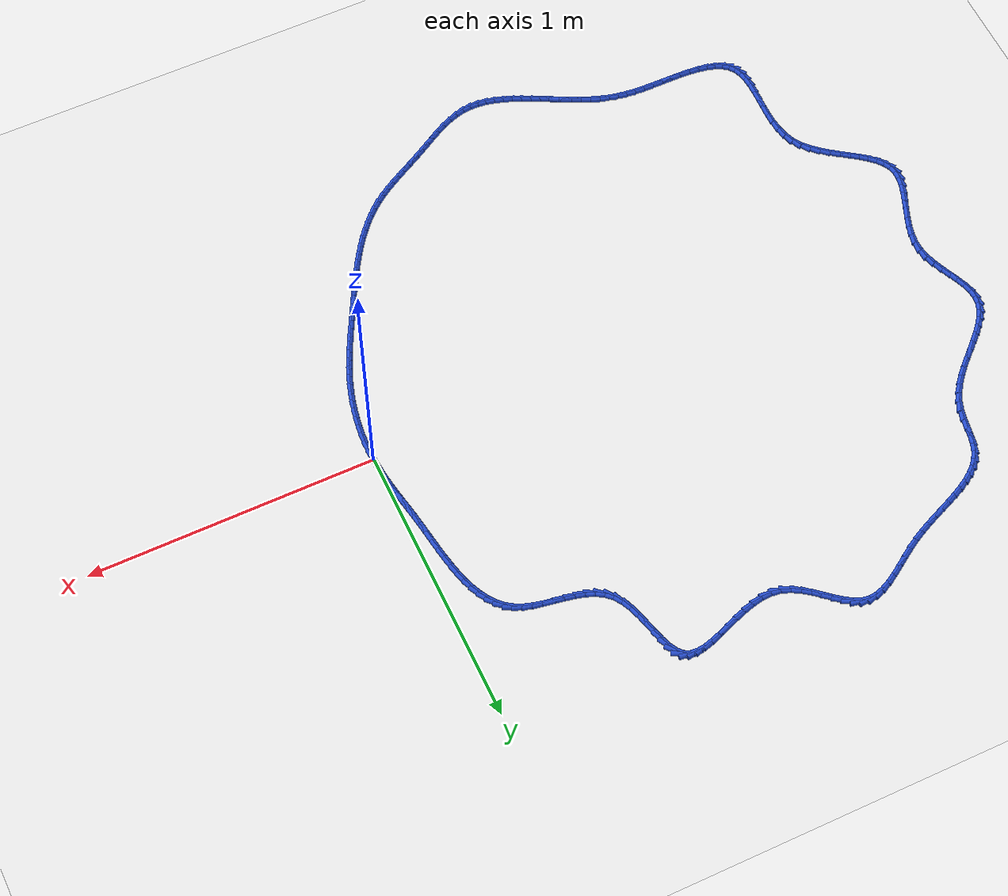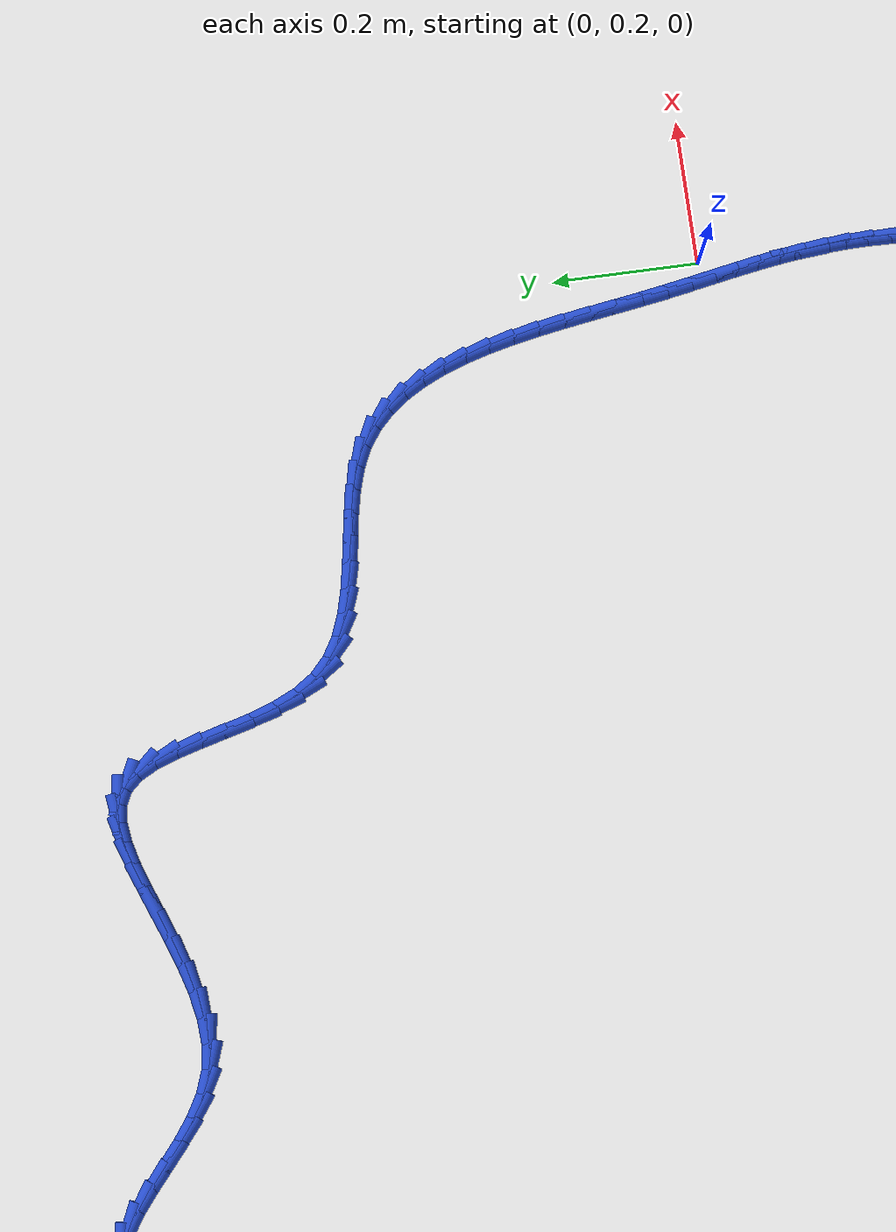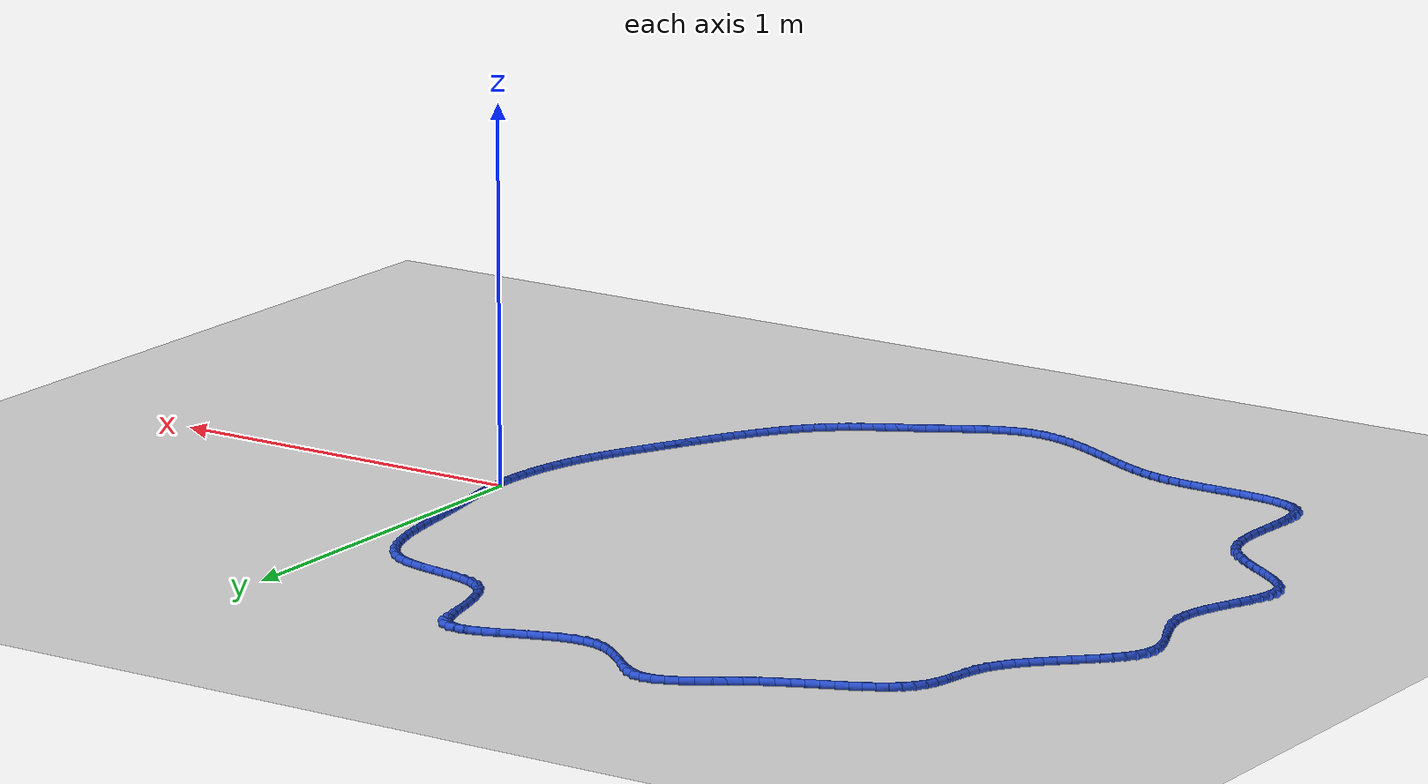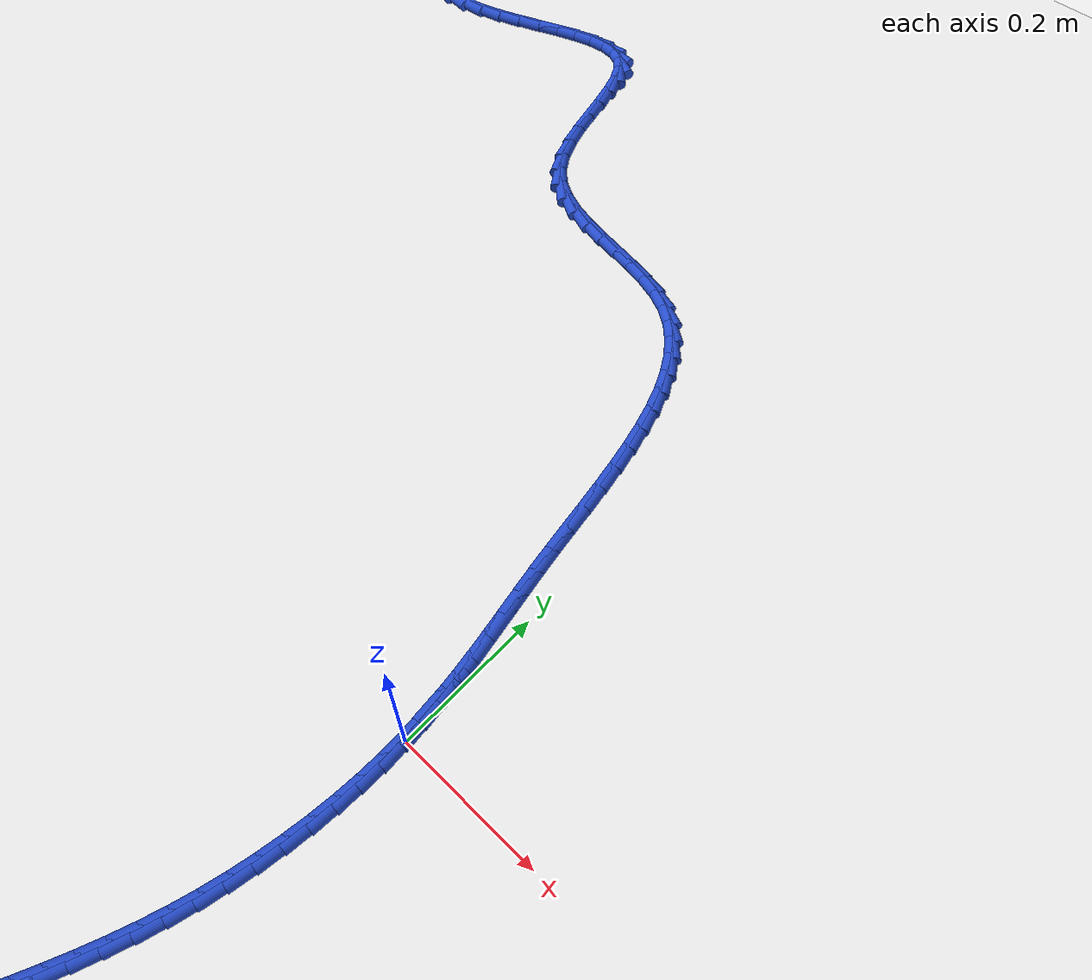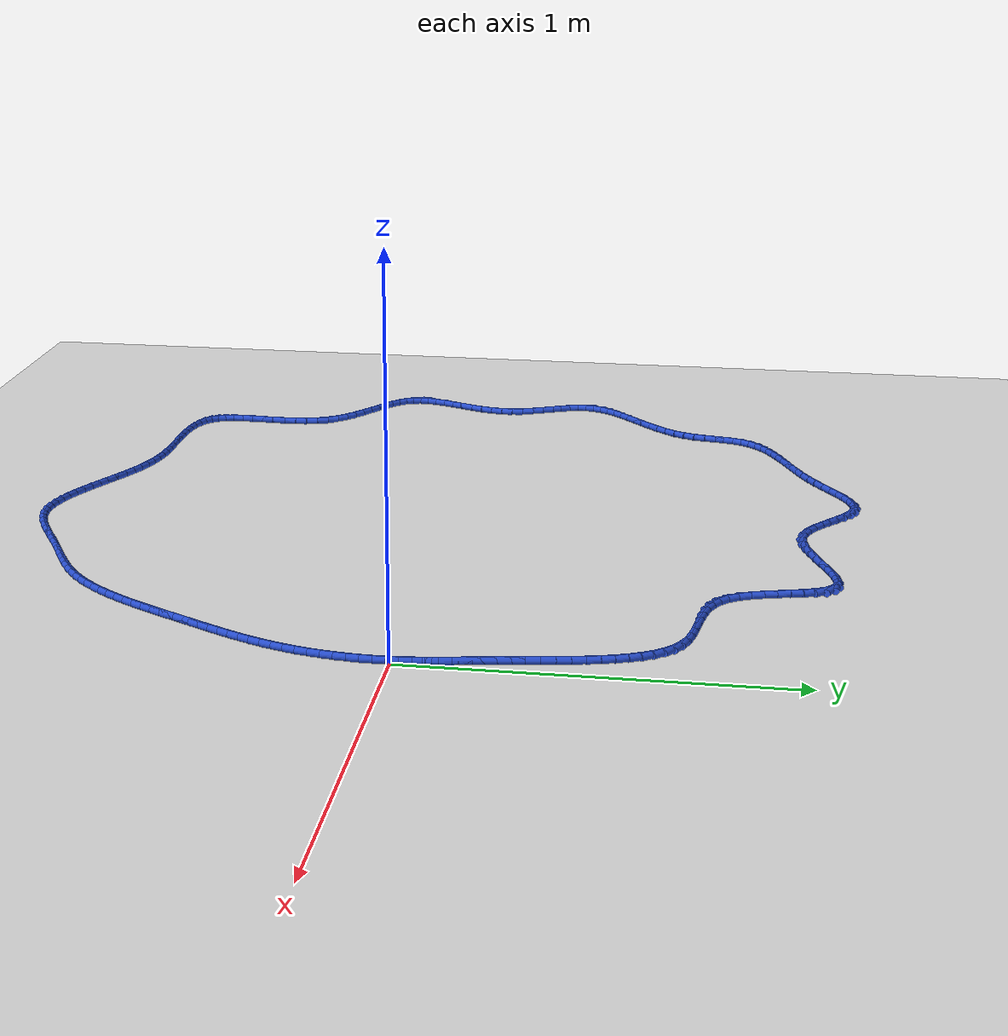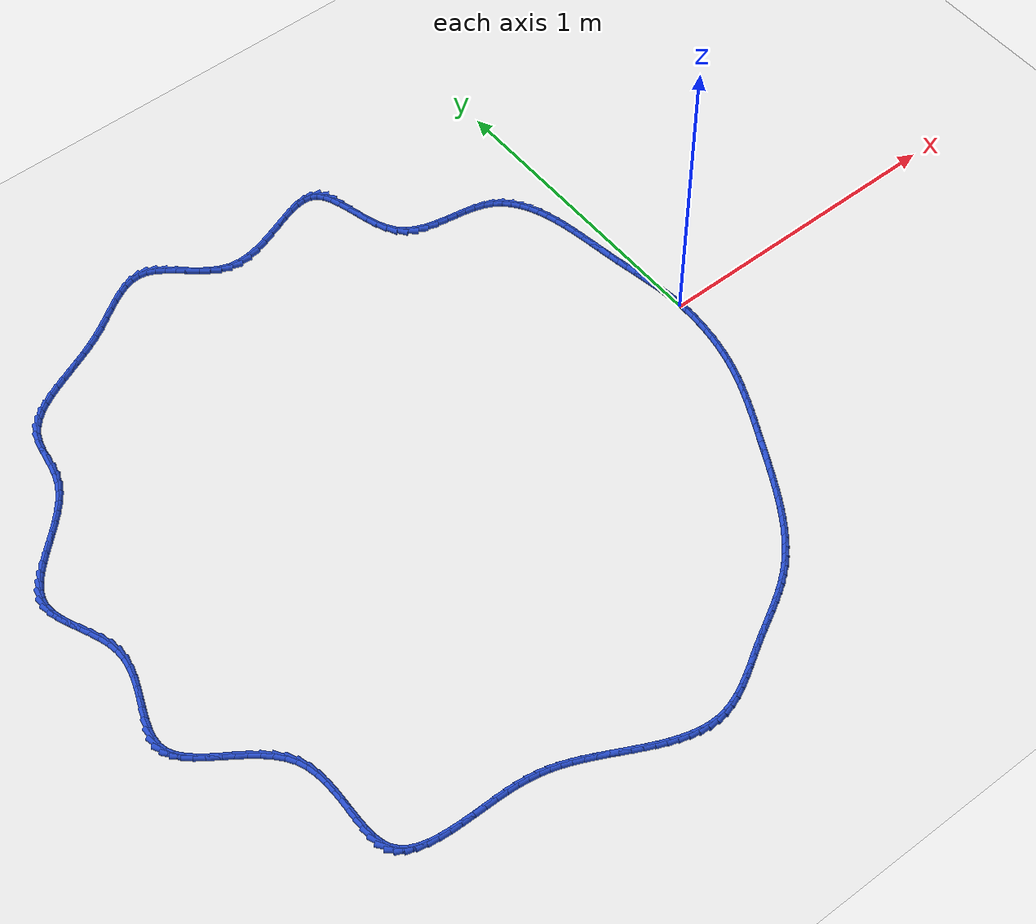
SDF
<sdf version="1.6">
 <world name="default">
  <light name="sun" type="directional">
   <pose>0 0 10 0 -0 0</pose>
   <diffuse>0.8 0.8 0.8 1</diffuse>
   <specular>0.2 0.2 0.2 1</specular>
   <attenuation>
    <range>1000</range>
    <constant>0.9</constant>
    <linear>0.01</linear>
    <quadratic>0.001</quadratic>
   </attenuation>
   <direction>-0.5 0.1 -0.9</direction>
  </light>
  <model name="ground_plane">
   <static>1</static>
   <link name="link">
    <collision name="collision">
     <geometry><plane><normal>0 0 1</normal><size>100 100</size></plane></geometry>
     <surface><friction><ode><mu>100</mu><mu2>50</mu2></ode></friction></surface>
    </collision>
    <visual name="visual">
     <cast_shadows>0</cast_shadows>
     <geometry><plane><normal>0 0 1</normal><size>100 100</size></plane></geometry>
     <material>
      <script><uri>file://media/materials/scripts/gazebo.material</uri><name>Gazebo/WhiteGlow</name></script>
     </material>
    </visual>
   </link>
  </model>
  <gravity>0 0 -9.8</gravity>
  <magnetic_field>6e-06 2.3e-05 -4.2e-05</magnetic_field>
  <atmosphere type="adiabatic"/>
  <physics name="default_physics" default="0" type="ode">
   <max_step_size>0.001</max_step_size>
   <real_time_factor>1</real_time_factor>
   <real_time_update_rate>1000</real_time_update_rate>
  </physics>
  <scene><ambient>0.4 0.4 0.4 1</ambient><background>0.7 0.7 0.7 1</background><shadows>1</shadows></scene>
  <spherical_coordinates>
   <surface_model>EARTH_WGS84</surface_model>
   <latitude_deg>0</latitude_deg>
   <longitude_deg>0</longitude_deg>
   <elevation>0</elevation>
   <heading_deg>0</heading_deg>
  </spherical_coordinates>
  <model name="line">
   <link name="link_0">
    <pose>-1.0408340855860843e-17 4.85722573273506e-17 0.01 0 1.57 -1.5140892674336408</pose>
    <collision name="collision">
     <geometry><cylinder><radius>0.01</radius><length>0.08</length></cylinder></geometry>
    </collision>
    <visual name="visual">
     <material>
      <script><name>Gazebo/Blue</name><uri>file://media/materials/scripts/gazebo.material</uri></script>
     </material>
     <geometry><cylinder><radius>0.01</radius><length>0.08</length></cylinder></geometry>
    </visual>
   </link>
   <link name="link_1">
    <pose>-0.0017822990523047434 0.0313962357053206 0.01 0 1.57 -1.4762455724888102</pose>
    <collision name="collision">
     <geometry><cylinder><radius>0.01</radius><length>0.08</length></cylinder></geometry>
    </collision>
    <visual name="visual">
     <material>
      <script><name>Gazebo/Blue</name><uri>file://media/materials/scripts/gazebo.material</uri></script>
     </material>
     <geometry><cylinder><radius>0.01</radius><length>0.08</length></cylinder></geometry>
    </visual>
   </link>
   <link name="link_2">
    <pose>-0.004735691657988238 0.06253915381352197 0.01 0 1.57 -1.4450884632466419</pose>
    <collision name="collision">
     <geometry><cylinder><radius>0.01</radius><length>0.08</length></cylinder></geometry>
    </collision>
    <visual name="visual">
     <material>
      <script><name>Gazebo/Blue</name><uri>file://media/materials/scripts/gazebo.material</uri></script>
     </material>
     <geometry><cylinder><radius>0.01</radius><length>0.08</length></cylinder></geometry>
    </visual>
   </link>
   <link name="link_3">
    <pose>-0.008661138716409207 0.09360123603166874 0.01 0 1.57 -1.4211090032281013</pose>
    <collision name="collision">
     <geometry><cylinder><radius>0.01</radius><length>0.08</length></cylinder></geometry>
    </collision>
    <visual name="visual">
     <material>
      <script><name>Gazebo/Blue</name><uri>file://media/materials/scripts/gazebo.material</uri></script>
     </material>
     <geometry><cylinder><radius>0.01</radius><length>0.08</length></cylinder></geometry>
    </visual>
   </link>
   <link name="link_4">
    <pose>-0.013359601126926387 0.12475496406682555 0.01 0 1.57 -1.40452897458954</pose>
    <collision name="collision">
     <geometry><cylinder><radius>0.01</radius><length>0.08</length></cylinder></geometry>
    </collision>
    <visual name="visual">
     <material>
      <script><name>Gazebo/Blue</name><uri>file://media/materials/scripts/gazebo.material</uri></script>
     </material>
     <geometry><cylinder><radius>0.01</radius><length>0.08</length></cylinder></geometry>
    </visual>
   </link>
   <link name="link_5">
    <pose>-0.018632039788898498 0.1561728196260569 0.01 0 1.57 -1.3953326870396339</pose>
    <collision name="collision">
     <geometry><cylinder><radius>0.01</radius><length>0.08</length></cylinder></geometry>
    </collision>
    <visual name="visual">
     <material>
      <script><name>Gazebo/Blue</name><uri>file://media/materials/scripts/gazebo.material</uri></script>
     </material>
     <geometry><cylinder><radius>0.01</radius><length>0.08</length></cylinder></geometry>
    </visual>
   </link>
   <link name="link_6">
    <pose>-0.024279415601684257 0.1880272844164274 0.01 0 1.57 -1.3933051526836118</pose>
    <collision name="collision">
     <geometry><cylinder><radius>0.01</radius><length>0.08</length></cylinder></geometry>
    </collision>
    <visual name="visual">
     <material>
      <script><name>Gazebo/Blue</name><uri>file://media/materials/scripts/gazebo.material</uri></script>
     </material>
     <geometry><cylinder><radius>0.01</radius><length>0.08</length></cylinder></geometry>
    </visual>
   </link>
   <link name="link_7">
    <pose>-0.030102689464642396 0.22049084014500175 0.01 0 1.57 -1.3980691826053695</pose>
    <collision name="collision">
     <geometry><cylinder><radius>0.01</radius><length>0.08</length></cylinder></geometry>
    </collision>
    <visual name="visual">
     <material>
      <script><name>Gazebo/Blue</name><uri>file://media/materials/scripts/gazebo.material</uri></script>
     </material>
     <geometry><cylinder><radius>0.01</radius><length>0.08</length></cylinder></geometry>
    </visual>
   </link>
   <link name="link_8">
    <pose>-0.035902822277131645 0.2537359685188444 0.01 0 1.57 -1.409102124069572</pose>
    <collision name="collision">
     <geometry><cylinder><radius>0.01</radius><length>0.08</length></cylinder></geometry>
    </collision>
    <visual name="visual">
     <material>
      <script><name>Gazebo/Blue</name><uri>file://media/materials/scripts/gazebo.material</uri></script>
     </material>
     <geometry><cylinder><radius>0.01</radius><length>0.08</length></cylinder></geometry>
    </visual>
   </link>
   <link name="link_9">
    <pose>-0.04148124559726623 0.287934611946852 0.01 0 1.57 -1.4214969574494418</pose>
    <collision name="collision">
     <geometry><cylinder><radius>0.01</radius><length>0.08</length></cylinder></geometry>
    </collision>
    <visual name="visual">
     <material>
      <script><name>Gazebo/Blue</name><uri>file://media/materials/scripts/gazebo.material</uri></script>
     </material>
     <geometry><cylinder><radius>0.01</radius><length>0.08</length></cylinder></geometry>
    </visual>
   </link>
   <link name="link_10">
    <pose>-0.046771823977987105 0.3231069662260764 0.01 0 1.57 -1.425215076478316</pose>
    <collision name="collision">
     <geometry><cylinder><radius>0.01</radius><length>0.08</length></cylinder></geometry>
    </collision>
    <visual name="visual">
     <material>
      <script><name>Gazebo/Blue</name><uri>file://media/materials/scripts/gazebo.material</uri></script>
     </material>
     <geometry><cylinder><radius>0.01</radius><length>0.08</length></cylinder></geometry>
    </visual>
   </link>
   <link name="link_11">
    <pose>-0.05202181707179196 0.35891412748517626 0.01 0 1.57 -1.4193484649039652</pose>
    <collision name="collision">
     <geometry><cylinder><radius>0.01</radius><length>0.08</length></cylinder></geometry>
    </collision>
    <visual name="visual">
     <material>
      <script><name>Gazebo/Blue</name><uri>file://media/materials/scripts/gazebo.material</uri></script>
     </material>
     <geometry><cylinder><radius>0.01</radius><length>0.08</length></cylinder></geometry>
    </visual>
   </link>
   <link name="link_12">
    <pose>-0.05752381283932963 0.3949652530048548 0.01 0 1.57 -1.4039532100160061</pose>
    <collision name="collision">
     <geometry><cylinder><radius>0.01</radius><length>0.08</length></cylinder></geometry>
    </collision>
    <visual name="visual">
     <material>
      <script><name>Gazebo/Blue</name><uri>file://media/materials/scripts/gazebo.material</uri></script>
     </material>
     <geometry><cylinder><radius>0.01</radius><length>0.08</length></cylinder></geometry>
    </visual>
   </link>
   <link name="link_13">
    <pose>-0.06357039924124894 0.4308695000658154 0.01 0 1.57 -1.378559220523546</pose>
    <collision name="collision">
     <geometry><cylinder><radius>0.01</radius><length>0.08</length></cylinder></geometry>
    </collision>
    <visual name="visual">
     <material>
      <script><name>Gazebo/Blue</name><uri>file://media/materials/scripts/gazebo.material</uri></script>
     </material>
     <geometry><cylinder><radius>0.01</radius><length>0.08</length></cylinder></geometry>
    </visual>
   </link>
   <link name="link_14">
    <pose>-0.07045416423819872 0.4662360259487611 0.01 0 1.57 -1.3421701288273173</pose>
    <collision name="collision">
     <geometry><cylinder><radius>0.01</radius><length>0.08</length></cylinder></geometry>
    </collision>
    <visual name="visual">
     <material>
      <script><name>Gazebo/Blue</name><uri>file://media/materials/scripts/gazebo.material</uri></script>
     </material>
     <geometry><cylinder><radius>0.01</radius><length>0.08</length></cylinder></geometry>
    </visual>
   </link>
   <link name="link_15">
    <pose>-0.07846769579082782 0.5006739879343955 0.01 0 1.57 -1.2932382194072782</pose>
    <collision name="collision">
     <geometry><cylinder><radius>0.01</radius><length>0.08</length></cylinder></geometry>
    </collision>
    <visual name="visual">
     <material>
      <script><name>Gazebo/Blue</name><uri>file://media/materials/scripts/gazebo.material</uri></script>
     </material>
     <geometry><cylinder><radius>0.01</radius><length>0.08</length></cylinder></geometry>
    </visual>
   </link>
   <link name="link_16">
    <pose>-0.0879035818597851 0.5337925433034216 0.01 0 1.57 -1.2296492479981362</pose>
    <collision name="collision">
     <geometry><cylinder><radius>0.01</radius><length>0.08</length></cylinder></geometry>
    </collision>
    <visual name="visual">
     <material>
      <script><name>Gazebo/Blue</name><uri>file://media/materials/scripts/gazebo.material</uri></script>
     </material>
     <geometry><cylinder><radius>0.01</radius><length>0.08</length></cylinder></geometry>
    </visual>
   </link>
   <link name="link_17">
    <pose>-0.09905441040571937 0.5652008493365427 0.01 0 1.57 -1.1487907853533612</pose>
    <collision name="collision">
     <geometry><cylinder><radius>0.01</radius><length>0.08</length></cylinder></geometry>
    </collision>
    <visual name="visual">
     <material>
      <script><name>Gazebo/Blue</name><uri>file://media/materials/scripts/gazebo.material</uri></script>
     </material>
     <geometry><cylinder><radius>0.01</radius><length>0.08</length></cylinder></geometry>
    </visual>
   </link>
   <link name="link_18">
    <pose>-0.11221276938927945 0.5945080633144622 0.01 0 1.57 -1.0478503527564522</pose>
    <collision name="collision">
     <geometry><cylinder><radius>0.01</radius><length>0.08</length></cylinder></geometry>
    </collision>
    <visual name="visual">
     <material>
      <script><name>Gazebo/Blue</name><uri>file://media/materials/scripts/gazebo.material</uri></script>
     </material>
     <geometry><cylinder><radius>0.01</radius><length>0.08</length></cylinder></geometry>
    </visual>
   </link>
   <link name="link_19">
    <pose>-0.1276712467711142 0.621323342517883 0.01 0 1.57 -0.924578249994057</pose>
    <collision name="collision">
     <geometry><cylinder><radius>0.01</radius><length>0.08</length></cylinder></geometry>
    </collision>
    <visual name="visual">
     <material>
      <script><name>Gazebo/Blue</name><uri>file://media/materials/scripts/gazebo.material</uri></script>
     </material>
     <geometry><cylinder><radius>0.01</radius><length>0.08</length></cylinder></geometry>
    </visual>
   </link>
   <link name="link_20">
    <pose>-0.14572243051187242 0.6452558442275088 0.01 0 1.57 -0.7787245237031976</pose>
    <collision name="collision">
     <geometry><cylinder><radius>0.01</radius><length>0.08</length></cylinder></geometry>
    </collision>
    <visual name="visual">
     <material>
      <script><name>Gazebo/Blue</name><uri>file://media/materials/scripts/gazebo.material</uri></script>
     </material>
     <geometry><cylinder><radius>0.01</radius><length>0.08</length></cylinder></geometry>
    </visual>
   </link>
   <link name="link_21">
    <pose>-0.16665890857220295 0.6659147257240425 0.01 0 1.57 -0.6139018739002147</pose>
    <collision name="collision">
     <geometry><cylinder><radius>0.01</radius><length>0.08</length></cylinder></geometry>
    </collision>
    <visual name="visual">
     <material>
      <script><name>Gazebo/Blue</name><uri>file://media/materials/scripts/gazebo.material</uri></script>
     </material>
     <geometry><cylinder><radius>0.01</radius><length>0.08</length></cylinder></geometry>
    </visual>
   </link>
   <link name="link_22">
    <pose>-0.1907732689127547 0.6829091442881876 0.01 0 1.57 -0.4415854745839687</pose>
    <collision name="collision">
     <geometry><cylinder><radius>0.01</radius><length>0.08</length></cylinder></geometry>
    </collision>
    <visual name="visual">
     <material>
      <script><name>Gazebo/Blue</name><uri>file://media/materials/scripts/gazebo.material</uri></script>
     </material>
     <geometry><cylinder><radius>0.01</radius><length>0.08</length></cylinder></geometry>
    </visual>
   </link>
   <link name="link_23">
    <pose>-0.21830001495683102 0.6959215559074463 0.01 0 1.57 -0.303847111143719</pose>
    <collision name="collision">
     <geometry><cylinder><radius>0.01</radius><length>0.08</length></cylinder></geometry>
    </collision>
    <visual name="visual">
     <material>
      <script><name>Gazebo/Blue</name><uri>file://media/materials/scripts/gazebo.material</uri></script>
     </material>
     <geometry><cylinder><radius>0.01</radius><length>0.08</length></cylinder></geometry>
    </visual>
   </link>
   <link name="link_24">
    <pose>-0.24879967724428598 0.7054849241748193 0.01 0 1.57 -0.21723763861743337</pose>
    <collision name="collision">
     <geometry><cylinder><radius>0.01</radius><length>0.08</length></cylinder></geometry>
    </collision>
    <visual name="visual">
     <material>
      <script><name>Gazebo/Blue</name><uri>file://media/materials/scripts/gazebo.material</uri></script>
     </material>
     <geometry><cylinder><radius>0.01</radius><length>0.08</length></cylinder></geometry>
    </visual>
   </link>
   <link name="link_25">
    <pose>-0.28139856258502693 0.7126801732821364 0.01 0 1.57 -0.1732210524831926</pose>
    <collision name="collision">
     <geometry><cylinder><radius>0.01</radius><length>0.08</length></cylinder></geometry>
    </collision>
    <visual name="visual">
     <material>
      <script><name>Gazebo/Blue</name><uri>file://media/materials/scripts/gazebo.material</uri></script>
     </material>
     <geometry><cylinder><radius>0.01</radius><length>0.08</length></cylinder></geometry>
    </visual>
   </link>
   <link name="link_26">
    <pose>-0.3152157675230457 0.7185973262828409 0.01 0 1.57 -0.16619235850822497</pose>
    <collision name="collision">
     <geometry><cylinder><radius>0.01</radius><length>0.08</length></cylinder></geometry>
    </collision>
    <visual name="visual">
     <material>
      <script><name>Gazebo/Blue</name><uri>file://media/materials/scripts/gazebo.material</uri></script>
     </material>
     <geometry><cylinder><radius>0.01</radius><length>0.08</length></cylinder></geometry>
    </visual>
   </link>
   <link name="link_27">
    <pose>-0.34937038860233427 0.7243264062303774 0.01 0 1.57 -0.19478526958126113</pose>
    <collision name="collision">
     <geometry><cylinder><radius>0.01</radius><length>0.08</length></cylinder></geometry>
    </collision>
    <visual name="visual">
     <material>
      <script><name>Gazebo/Blue</name><uri>file://media/materials/scripts/gazebo.material</uri></script>
     </material>
     <geometry><cylinder><radius>0.01</radius><length>0.08</length></cylinder></geometry>
    </visual>
   </link>
   <link name="link_28">
    <pose>-0.38298152236688415 0.730957436178189 0.01 0 1.57 -0.261758550055799</pose>
    <collision name="collision">
     <geometry><cylinder><radius>0.01</radius><length>0.08</length></cylinder></geometry>
    </collision>
    <visual name="visual">
     <material>
      <script><name>Gazebo/Blue</name><uri>file://media/materials/scripts/gazebo.material</uri></script>
     </material>
     <geometry><cylinder><radius>0.01</radius><length>0.08</length></cylinder></geometry>
    </visual>
   </link>
   <link name="link_29">
    <pose>-0.4151682653606876 0.7395804391797203 0.01 0 1.57 -0.37334342968593964</pose>
    <collision name="collision">
     <geometry><cylinder><radius>0.01</radius><length>0.08</length></cylinder></geometry>
    </collision>
    <visual name="visual">
     <material>
      <script><name>Gazebo/Blue</name><uri>file://media/materials/scripts/gazebo.material</uri></script>
     </material>
     <geometry><cylinder><radius>0.01</radius><length>0.08</length></cylinder></geometry>
    </visual>
   </link>
   <link name="link_30">
    <pose>-0.4450497141277363 0.7512854382884149 0.01 0 1.57 -0.5365507530079408</pose>
    <collision name="collision">
     <geometry><cylinder><radius>0.01</radius><length>0.08</length></cylinder></geometry>
    </collision>
    <visual name="visual">
     <material>
      <script><name>Gazebo/Blue</name><uri>file://media/materials/scripts/gazebo.material</uri></script>
     </material>
     <geometry><cylinder><radius>0.01</radius><length>0.08</length></cylinder></geometry>
    </visual>
   </link>
   <link name="link_31">
    <pose>-0.47174496521202197 0.7671624565577166 0.01 0 1.57 -0.751378900271499</pose>
    <collision name="collision">
     <geometry><cylinder><radius>0.01</radius><length>0.08</length></cylinder></geometry>
    </collision>
    <visual name="visual">
     <material>
      <script><name>Gazebo/Blue</name><uri>file://media/materials/scripts/gazebo.material</uri></script>
     </material>
     <geometry><cylinder><radius>0.01</radius><length>0.08</length></cylinder></geometry>
    </visual>
   </link>
   <link name="link_32">
    <pose>-0.49437328444214507 0.7883012753539985 0.01 0 1.57 -0.9794375298426329</pose>
    <collision name="collision">
     <geometry><cylinder><radius>0.01</radius><length>0.08</length></cylinder></geometry>
    </collision>
    <visual name="visual">
     <material>
      <script><name>Gazebo/Blue</name><uri>file://media/materials/scripts/gazebo.material</uri></script>
     </material>
     <geometry><cylinder><radius>0.01</radius><length>0.08</length></cylinder></geometry>
    </visual>
   </link>
   <link name="link_33">
    <pose>-0.512452076773353 0.815223254139059 0.01 0 1.57 -1.144041291427519</pose>
    <collision name="collision">
     <geometry><cylinder><radius>0.01</radius><length>0.08</length></cylinder></geometry>
    </collision>
    <visual name="visual">
     <material>
      <script><name>Gazebo/Blue</name><uri>file://media/materials/scripts/gazebo.material</uri></script>
     </material>
     <geometry><cylinder><radius>0.01</radius><length>0.08</length></cylinder></geometry>
    </visual>
   </link>
   <link name="link_34">
    <pose>-0.5267487053594899 0.846665191219239 0.01 0 1.57 -1.2470378099294164</pose>
    <collision name="collision">
     <geometry><cylinder><radius>0.01</radius><length>0.08</length></cylinder></geometry>
    </collision>
    <visual name="visual">
     <material>
      <script><name>Gazebo/Blue</name><uri>file://media/materials/scripts/gazebo.material</uri></script>
     </material>
     <geometry><cylinder><radius>0.01</radius><length>0.08</length></cylinder></geometry>
    </visual>
   </link>
   <link name="link_35">
    <pose>-0.5382751914088753 0.8810145874116686 0.01 0 1.57 -1.3033127828432685</pose>
    <collision name="collision">
     <geometry><cylinder><radius>0.01</radius><length>0.08</length></cylinder></geometry>
    </collision>
    <visual name="visual">
     <material>
      <script><name>Gazebo/Blue</name><uri>file://media/materials/scripts/gazebo.material</uri></script>
     </material>
     <geometry><cylinder><radius>0.01</radius><length>0.08</length></cylinder></geometry>
    </visual>
   </link>
   <link name="link_36">
    <pose>-0.5480435561298285 0.9166589435334778 0.01 0 1.57 -1.3207472361059984</pose>
    <collision name="collision">
     <geometry><cylinder><radius>0.01</radius><length>0.08</length></cylinder></geometry>
    </collision>
    <visual name="visual">
     <material>
      <script><name>Gazebo/Blue</name><uri>file://media/materials/scripts/gazebo.material</uri></script>
     </material>
     <geometry><cylinder><radius>0.01</radius><length>0.08</length></cylinder></geometry>
    </visual>
   </link>
   <link name="link_37">
    <pose>-0.5570658207306691 0.9519857604017972 0.01 0 1.57 -1.2995353078400214</pose>
    <collision name="collision">
     <geometry><cylinder><radius>0.01</radius><length>0.08</length></cylinder></geometry>
    </collision>
    <visual name="visual">
     <material>
      <script><name>Gazebo/Blue</name><uri>file://media/materials/scripts/gazebo.material</uri></script>
     </material>
     <geometry><cylinder><radius>0.01</radius><length>0.08</length></cylinder></geometry>
    </visual>
   </link>
   <link name="link_38">
    <pose>-0.566354006419717 0.985382538833757 0.01 0 1.57 -1.2306301543189473</pose>
    <collision name="collision">
     <geometry><cylinder><radius>0.01</radius><length>0.08</length></cylinder></geometry>
    </collision>
    <visual name="visual">
     <material>
      <script><name>Gazebo/Blue</name><uri>file://media/materials/scripts/gazebo.material</uri></script>
     </material>
     <geometry><cylinder><radius>0.01</radius><length>0.08</length></cylinder></geometry>
    </visual>
   </link>
   <link name="link_39">
    <pose>-0.5769201344052914 1.0152367796464876 0.01 0 1.57 -1.0908785751996821</pose>
    <collision name="collision">
     <geometry><cylinder><radius>0.01</radius><length>0.08</length></cylinder></geometry>
    </collision>
    <visual name="visual">
     <material>
      <script><name>Gazebo/Blue</name><uri>file://media/materials/scripts/gazebo.material</uri></script>
     </material>
     <geometry><cylinder><radius>0.01</radius><length>0.08</length></cylinder></geometry>
    </visual>
   </link>
   <link name="link_40">
    <pose>-0.589776225895712 1.039935983657119 0.01 0 1.57 -0.8373784345812626</pose>
    <collision name="collision">
     <geometry><cylinder><radius>0.01</radius><length>0.08</length></cylinder></geometry>
    </collision>
    <visual name="visual">
     <material>
      <script><name>Gazebo/Blue</name><uri>file://media/materials/scripts/gazebo.material</uri></script>
     </material>
     <geometry><cylinder><radius>0.01</radius><length>0.08</length></cylinder></geometry>
    </visual>
   </link>
   <link name="link_41">
    <pose>-0.6059343020992981 1.0578676516827814 0.01 0 1.57 -0.4551619494992559</pose>
    <collision name="collision">
     <geometry><cylinder><radius>0.01</radius><length>0.08</length></cylinder></geometry>
    </collision>
    <visual name="visual">
     <material>
      <script><name>Gazebo/Blue</name><uri>file://media/materials/scripts/gazebo.material</uri></script>
     </material>
     <geometry><cylinder><radius>0.01</radius><length>0.08</length></cylinder></geometry>
    </visual>
   </link>
   <link name="link_42">
    <pose>-0.6262105241636294 1.0677915948566767 0.01 0 1.57 -0.10840177283015996</pose>
    <collision name="collision">
     <geometry><cylinder><radius>0.01</radius><length>0.08</length></cylinder></geometry>
    </collision>
    <visual name="visual">
     <material>
      <script><name>Gazebo/Blue</name><uri>file://media/materials/scripts/gazebo.material</uri></script>
     </material>
     <geometry><cylinder><radius>0.01</radius><length>0.08</length></cylinder></geometry>
    </visual>
   </link>
   <link name="link_43">
    <pose>-0.6503922614195509 1.0704232542909442 0.01 0 1.57 0.11945580834634709</pose>
    <collision name="collision">
     <geometry><cylinder><radius>0.01</radius><length>0.08</length></cylinder></geometry>
    </collision>
    <visual name="visual">
     <material>
      <script><name>Gazebo/Blue</name><uri>file://media/materials/scripts/gazebo.material</uri></script>
     </material>
     <geometry><cylinder><radius>0.01</radius><length>0.08</length></cylinder></geometry>
    </visual>
   </link>
   <link name="link_44">
    <pose>-0.6779302681394077 1.0671179425362949 0.01 0 1.57 0.2542738200076538</pose>
    <collision name="collision">
     <geometry><cylinder><radius>0.01</radius><length>0.08</length></cylinder></geometry>
    </collision>
    <visual name="visual">
     <material>
      <script><name>Gazebo/Blue</name><uri>file://media/materials/scripts/gazebo.material</uri></script>
     </material>
     <geometry><cylinder><radius>0.01</radius><length>0.08</length></cylinder></geometry>
    </visual>
   </link>
   <link name="link_45">
    <pose>-0.708275106404956 1.0592313374784559 0.01 0 1.57 0.32849335379676337</pose>
    <collision name="collision">
     <geometry><cylinder><radius>0.01</radius><length>0.08</length></cylinder></geometry>
    </collision>
    <visual name="visual">
     <material>
      <script><name>Gazebo/Blue</name><uri>file://media/materials/scripts/gazebo.material</uri></script>
     </material>
     <geometry><cylinder><radius>0.01</radius><length>0.08</length></cylinder></geometry>
    </visual>
   </link>
   <link name="link_46">
    <pose>-0.7408773382979535 1.0481191170031552 0.01 0 1.57 0.36172732578223527</pose>
    <collision name="collision">
     <geometry><cylinder><radius>0.01</radius><length>0.08</length></cylinder></geometry>
    </collision>
    <visual name="visual">
     <material>
      <script><name>Gazebo/Blue</name><uri>file://media/materials/scripts/gazebo.material</uri></script>
     </material>
     <geometry><cylinder><radius>0.01</radius><length>0.08</length></cylinder></geometry>
    </visual>
   </link>
   <link name="link_47">
    <pose>-0.7751875259001574 1.0351369589961203 0.01 0 1.57 0.36359801487771587</pose>
    <collision name="collision">
     <geometry><cylinder><radius>0.01</radius><length>0.08</length></cylinder></geometry>
    </collision>
    <visual name="visual">
     <material>
      <script><name>Gazebo/Blue</name><uri>file://media/materials/scripts/gazebo.material</uri></script>
     </material>
     <geometry><cylinder><radius>0.01</radius><length>0.08</length></cylinder></geometry>
    </visual>
   </link>
   <link name="link_48">
    <pose>-0.8106562312933241 1.0216405413430785 0.01 0 1.57 0.3373604920326366</pose>
    <collision name="collision">
     <geometry><cylinder><radius>0.01</radius><length>0.08</length></cylinder></geometry>
    </collision>
    <visual name="visual">
     <material>
      <script><name>Gazebo/Blue</name><uri>file://media/materials/scripts/gazebo.material</uri></script>
     </material>
     <geometry><cylinder><radius>0.01</radius><length>0.08</length></cylinder></geometry>
    </visual>
   </link>
   <link name="link_49">
    <pose>-0.8467340165592113 1.0089855419297573 0.01 0 1.57 0.28169703186375755</pose>
    <collision name="collision">
     <geometry><cylinder><radius>0.01</radius><length>0.08</length></cylinder></geometry>
    </collision>
    <visual name="visual">
     <material>
      <script><name>Gazebo/Blue</name><uri>file://media/materials/scripts/gazebo.material</uri></script>
     </material>
     <geometry><cylinder><radius>0.01</radius><length>0.08</length></cylinder></geometry>
    </visual>
   </link>
   <link name="link_50">
    <pose>-0.8828714437795754 0.998527638641884 0.01 0 1.57 0.1913355445748253</pose>
    <collision name="collision">
     <geometry><cylinder><radius>0.01</radius><length>0.08</length></cylinder></geometry>
    </collision>
    <visual name="visual">
     <material>
      <script><name>Gazebo/Blue</name><uri>file://media/materials/scripts/gazebo.material</uri></script>
     </material>
     <geometry><cylinder><radius>0.01</radius><length>0.08</length></cylinder></geometry>
    </visual>
   </link>
   <link name="link_51">
    <pose>-0.9185190750361738 0.9916225093651863 0.01 0 1.57 0.05762955264114487</pose>
    <collision name="collision">
     <geometry><cylinder><radius>0.01</radius><length>0.08</length></cylinder></geometry>
    </collision>
    <visual name="visual">
     <material>
      <script><name>Gazebo/Blue</name><uri>file://media/materials/scripts/gazebo.material</uri></script>
     </material>
     <geometry><cylinder><radius>0.01</radius><length>0.08</length></cylinder></geometry>
    </visual>
   </link>
   <link name="link_52">
    <pose>-0.9531274724107635 0.9896258319853914 0.01 0 1.57 -0.1285162788359451</pose>
    <collision name="collision">
     <geometry><cylinder><radius>0.01</radius><length>0.08</length></cylinder></geometry>
    </collision>
    <visual name="visual">
     <material>
      <script><name>Gazebo/Blue</name><uri>file://media/materials/scripts/gazebo.material</uri></script>
     </material>
     <geometry><cylinder><radius>0.01</radius><length>0.08</length></cylinder></geometry>
    </visual>
   </link>
   <link name="link_53">
    <pose>-0.9861472942064398 0.9938929349600233 0.01 0 1.57 -0.346181371847614</pose>
    <collision name="collision">
     <geometry><cylinder><radius>0.01</radius><length>0.08</length></cylinder></geometry>
    </collision>
    <visual name="visual">
     <material>
      <script><name>Gazebo/Blue</name><uri>file://media/materials/scripts/gazebo.material</uri></script>
     </material>
     <geometry><cylinder><radius>0.01</radius><length>0.08</length></cylinder></geometry>
    </visual>
   </link>
   <link name="link_54">
    <pose>-1.017216285767238 1.0050997393516479 0.01 0 1.57 -0.5182064989716741</pose>
    <collision name="collision">
     <geometry><cylinder><radius>0.01</radius><length>0.08</length></cylinder></geometry>
    </collision>
    <visual name="visual">
     <material>
      <script><name>Gazebo/Blue</name><uri>file://media/materials/scripts/gazebo.material</uri></script>
     </material>
     <geometry><cylinder><radius>0.01</radius><length>0.08</length></cylinder></geometry>
    </visual>
   </link>
   <link name="link_55">
    <pose>-1.046549651702975 1.021825120412035 0.01 0 1.57 -0.6313944586313898</pose>
    <collision name="collision">
     <geometry><cylinder><radius>0.01</radius><length>0.08</length></cylinder></geometry>
    </collision>
    <visual name="visual">
     <material>
      <script><name>Gazebo/Blue</name><uri>file://media/materials/scripts/gazebo.material</uri></script>
     </material>
     <geometry><cylinder><radius>0.01</radius><length>0.08</length></cylinder></geometry>
    </visual>
   </link>
   <link name="link_56">
    <pose>-1.0744736600601417 1.0422446260443186 0.01 0 1.57 -0.6930151942540611</pose>
    <collision name="collision">
     <geometry><cylinder><radius>0.01</radius><length>0.08</length></cylinder></geometry>
    </collision>
    <visual name="visual">
     <material>
      <script><name>Gazebo/Blue</name><uri>file://media/materials/scripts/gazebo.material</uri></script>
     </material>
     <geometry><cylinder><radius>0.01</radius><length>0.08</length></cylinder></geometry>
    </visual>
   </link>
   <link name="link_57">
    <pose>-1.1013145788852308 1.0645338041516346 0.01 0 1.57 -0.7081089089771929</pose>
    <collision name="collision">
     <geometry><cylinder><radius>0.01</radius><length>0.08</length></cylinder></geometry>
    </collision>
    <visual name="visual">
     <material>
      <script><name>Gazebo/Blue</name><uri>file://media/materials/scripts/gazebo.material</uri></script>
     </material>
     <geometry><cylinder><radius>0.01</radius><length>0.08</length></cylinder></geometry>
    </visual>
   </link>
   <link name="link_58">
    <pose>-1.127398676224733 1.0868682026371166 0.01 0 1.57 -0.675508957044422</pose>
    <collision name="collision">
     <geometry><cylinder><radius>0.01</radius><length>0.08</length></cylinder></geometry>
    </collision>
    <visual name="visual">
     <material>
      <script><name>Gazebo/Blue</name><uri>file://media/materials/scripts/gazebo.material</uri></script>
     </material>
     <geometry><cylinder><radius>0.01</radius><length>0.08</length></cylinder></geometry>
    </visual>
   </link>
   <link name="link_59">
    <pose>-1.1530522201251399 1.1074233694039002 0.01 0 1.57 -0.5857948592822503</pose>
    <collision name="collision">
     <geometry><cylinder><radius>0.01</radius><length>0.08</length></cylinder></geometry>
    </collision>
    <visual name="visual">
     <material>
      <script><name>Gazebo/Blue</name><uri>file://media/materials/scripts/gazebo.material</uri></script>
     </material>
     <geometry><cylinder><radius>0.01</radius><length>0.08</length></cylinder></geometry>
    </visual>
   </link>
   <link name="link_60">
    <pose>-1.178601478632944 1.1243748523551196 0.01 0 1.57 -0.42047281858697133</pose>
    <collision name="collision">
     <geometry><cylinder><radius>0.01</radius><length>0.08</length></cylinder></geometry>
    </collision>
    <visual name="visual">
     <material>
      <script><name>Gazebo/Blue</name><uri>file://media/materials/scripts/gazebo.material</uri></script>
     </material>
     <geometry><cylinder><radius>0.01</radius><length>0.08</length></cylinder></geometry>
    </visual>
   </link>
   <link name="link_61">
    <pose>-1.204372719794636 1.1358981993939101 0.01 0 1.57 -0.16664006665563905</pose>
    <collision name="collision">
     <geometry><cylinder><radius>0.01</radius><length>0.08</length></cylinder></geometry>
    </collision>
    <visual name="visual">
     <material>
      <script><name>Gazebo/Blue</name><uri>file://media/materials/scripts/gazebo.material</uri></script>
     </material>
     <geometry><cylinder><radius>0.01</radius><length>0.08</length></cylinder></geometry>
    </visual>
   </link>
   <link name="link_62">
    <pose>-1.2306767790470252 1.1403225386254945 0.01 0 1.57 0.09670289515217058</pose>
    <collision name="collision">
     <geometry><cylinder><radius>0.01</radius><length>0.08</length></cylinder></geometry>
    </collision>
    <visual name="visual">
     <material>
      <script><name>Gazebo/Blue</name><uri>file://media/materials/scripts/gazebo.material</uri></script>
     </material>
     <geometry><cylinder><radius>0.01</radius><length>0.08</length></cylinder></geometry>
    </visual>
   </link>
   <link name="link_63">
    <pose>-1.2576507604541767 1.1377059150319855 0.01 0 1.57 0.29836750721970856</pose>
    <collision name="collision">
     <geometry><cylinder><radius>0.01</radius><length>0.08</length></cylinder></geometry>
    </collision>
    <visual name="visual">
     <material>
      <script><name>Gazebo/Blue</name><uri>file://media/materials/scripts/gazebo.material</uri></script>
     </material>
     <geometry><cylinder><radius>0.01</radius><length>0.08</length></cylinder></geometry>
    </visual>
   </link>
   <link name="link_64">
    <pose>-1.2853223194434207 1.1291955700498728 0.01 0 1.57 0.4363025226950645</pose>
    <collision name="collision">
     <geometry><cylinder><radius>0.01</radius><length>0.08</length></cylinder></geometry>
    </collision>
    <visual name="visual">
     <material>
      <script><name>Gazebo/Blue</name><uri>file://media/materials/scripts/gazebo.material</uri></script>
     </material>
     <geometry><cylinder><radius>0.01</radius><length>0.08</length></cylinder></geometry>
    </visual>
   </link>
   <link name="link_65">
    <pose>-1.3137174021578213 1.1159557553445159 0.01 0 1.57 0.5230431974243606</pose>
    <collision name="collision">
     <geometry><cylinder><radius>0.01</radius><length>0.08</length></cylinder></geometry>
    </collision>
    <visual name="visual">
     <material>
      <script><name>Gazebo/Blue</name><uri>file://media/materials/scripts/gazebo.material</uri></script>
     </material>
     <geometry><cylinder><radius>0.01</radius><length>0.08</length></cylinder></geometry>
    </visual>
   </link>
   <link name="link_66">
    <pose>-1.3428619547404441 1.0991507225812764 0.01 0 1.57 0.570668717510265</pose>
    <collision name="collision">
     <geometry><cylinder><radius>0.01</radius><length>0.08</length></cylinder></geometry>
    </collision>
    <visual name="visual">
     <material>
      <script><name>Gazebo/Blue</name><uri>file://media/materials/scripts/gazebo.material</uri></script>
     </material>
     <geometry><cylinder><radius>0.01</radius><length>0.08</length></cylinder></geometry>
    </visual>
   </link>
   <link name="link_67">
    <pose>-1.3727819233343534 1.0799447234255148 0.01 0 1.57 0.5871418721030882</pose>
    <collision name="collision">
     <geometry><cylinder><radius>0.01</radius><length>0.08</length></cylinder></geometry>
    </collision>
    <visual name="visual">
     <material>
      <script><name>Gazebo/Blue</name><uri>file://media/materials/scripts/gazebo.material</uri></script>
     </material>
     <geometry><cylinder><radius>0.01</radius><length>0.08</length></cylinder></geometry>
    </visual>
   </link>
   <link name="link_68">
    <pose>-1.4035032540826147 1.059502009542592 0.01 0 1.57 0.576565971405068</pose>
    <collision name="collision">
     <geometry><cylinder><radius>0.01</radius><length>0.08</length></cylinder></geometry>
    </collision>
    <visual name="visual">
     <material>
      <script><name>Gazebo/Blue</name><uri>file://media/materials/scripts/gazebo.material</uri></script>
     </material>
     <geometry><cylinder><radius>0.01</radius><length>0.08</length></cylinder></geometry>
    </visual>
   </link>
   <link name="link_69">
    <pose>-1.4350518931282918 1.0389868325978686 0.01 0 1.57 0.5400562445148892</pose>
    <collision name="collision">
     <geometry><cylinder><radius>0.01</radius><length>0.08</length></cylinder></geometry>
    </collision>
    <visual name="visual">
     <material>
      <script><name>Gazebo/Blue</name><uri>file://media/materials/scripts/gazebo.material</uri></script>
     </material>
     <geometry><cylinder><radius>0.01</radius><length>0.08</length></cylinder></geometry>
    </visual>
   </link>
   <link name="link_70">
    <pose>-1.4674533755316481 1.0195619469024544 0.01 0 1.57 0.48790147113323207</pose>
    <collision name="collision">
     <geometry><cylinder><radius>0.01</radius><length>0.08</length></cylinder></geometry>
    </collision>
    <visual name="visual">
     <material>
      <script><name>Gazebo/Blue</name><uri>file://media/materials/scripts/gazebo.material</uri></script>
     </material>
     <geometry><cylinder><radius>0.01</radius><length>0.08</length></cylinder></geometry>
    </visual>
   </link>
   <link name="link_71">
    <pose>-1.500615906725987 1.001962737841111 0.01 0 1.57 0.44622824751929685</pose>
    <collision name="collision">
     <geometry><cylinder><radius>0.01</radius><length>0.08</length></cylinder></geometry>
    </collision>
    <visual name="visual">
     <material>
      <script><name>Gazebo/Blue</name><uri>file://media/materials/scripts/gazebo.material</uri></script>
     </material>
     <geometry><cylinder><radius>0.01</radius><length>0.08</length></cylinder></geometry>
    </visual>
   </link>
   <link name="link_72">
    <pose>-1.5341692627238495 0.9859104216948652 0.01 0 1.57 0.41891009373407645</pose>
    <collision name="collision">
     <geometry><cylinder><radius>0.01</radius><length>0.08</length></cylinder></geometry>
    </collision>
    <visual name="visual">
     <material>
      <script><name>Gazebo/Blue</name><uri>file://media/materials/scripts/gazebo.material</uri></script>
     </material>
     <geometry><cylinder><radius>0.01</radius><length>0.08</length></cylinder></geometry>
    </visual>
   </link>
   <link name="link_73">
    <pose>-1.5677028225978227 0.9709790703507528 0.01 0 1.57 0.40614810938967394</pose>
    <collision name="collision">
     <geometry><cylinder><radius>0.01</radius><length>0.08</length></cylinder></geometry>
    </collision>
    <visual name="visual">
     <material>
      <script><name>Gazebo/Blue</name><uri>file://media/materials/scripts/gazebo.material</uri></script>
     </material>
     <geometry><cylinder><radius>0.01</radius><length>0.08</length></cylinder></geometry>
    </visual>
   </link>
   <link name="link_74">
    <pose>-1.6008059654204922 0.9567427556958079 0.01 0 1.57 0.4085675052500353</pose>
    <collision name="collision">
     <geometry><cylinder><radius>0.01</radius><length>0.08</length></cylinder></geometry>
    </collision>
    <visual name="visual">
     <material>
      <script><name>Gazebo/Blue</name><uri>file://media/materials/scripts/gazebo.material</uri></script>
     </material>
     <geometry><cylinder><radius>0.01</radius><length>0.08</length></cylinder></geometry>
    </visual>
   </link>
   <link name="link_75">
    <pose>-1.6330680702644442 0.9427755496170654 0.01 0 1.57 0.4273853883662749</pose>
    <collision name="collision">
     <geometry><cylinder><radius>0.01</radius><length>0.08</length></cylinder></geometry>
    </collision>
    <visual name="visual">
     <material>
      <script><name>Gazebo/Blue</name><uri>file://media/materials/scripts/gazebo.material</uri></script>
     </material>
     <geometry><cylinder><radius>0.01</radius><length>0.08</length></cylinder></geometry>
    </visual>
   </link>
   <link name="link_76">
    <pose>-1.6640785162022662 0.9286515240015599 0.01 0 1.57 0.46453831258176576</pose>
    <collision name="collision">
     <geometry><cylinder><radius>0.01</radius><length>0.08</length></cylinder></geometry>
    </collision>
    <visual name="visual">
     <material>
      <script><name>Gazebo/Blue</name><uri>file://media/materials/scripts/gazebo.material</uri></script>
     </material>
     <geometry><cylinder><radius>0.01</radius><length>0.08</length></cylinder></geometry>
    </visual>
   </link>
   <link name="link_77">
    <pose>-1.6934266823065436 0.9139447507363267 0.01 0 1.57 0.5227202612666265</pose>
    <collision name="collision">
     <geometry><cylinder><radius>0.01</radius><length>0.08</length></cylinder></geometry>
    </collision>
    <visual name="visual">
     <material>
      <script><name>Gazebo/Blue</name><uri>file://media/materials/scripts/gazebo.material</uri></script>
     </material>
     <geometry><cylinder><radius>0.01</radius><length>0.08</length></cylinder></geometry>
    </visual>
   </link>
   <link name="link_78">
    <pose>-1.7207019476498626 0.8982293017083997 0.01 0 1.57 0.6051775018354557</pose>
    <collision name="collision">
     <geometry><cylinder><radius>0.01</radius><length>0.08</length></cylinder></geometry>
    </collision>
    <visual name="visual">
     <material>
      <script><name>Gazebo/Blue</name><uri>file://media/materials/scripts/gazebo.material</uri></script>
     </material>
     <geometry><cylinder><radius>0.01</radius><length>0.08</length></cylinder></geometry>
    </visual>
   </link>
   <link name="link_79">
    <pose>-1.74549369130481 0.8810792488048139 0.01 0 1.57 0.7149419119155603</pose>
    <collision name="collision">
     <geometry><cylinder><radius>0.01</radius><length>0.08</length></cylinder></geometry>
    </collision>
    <visual name="visual">
     <material>
      <script><name>Gazebo/Blue</name><uri>file://media/materials/scripts/gazebo.material</uri></script>
     </material>
     <geometry><cylinder><radius>0.01</radius><length>0.08</length></cylinder></geometry>
    </visual>
   </link>
   <link name="link_80">
    <pose>-1.7673912923439716 0.8620686639126041 0.01 0 1.57 0.8530864119545841</pose>
    <collision name="collision">
     <geometry><cylinder><radius>0.01</radius><length>0.08</length></cylinder></geometry>
    </collision>
    <visual name="visual">
     <material>
      <script><name>Gazebo/Blue</name><uri>file://media/materials/scripts/gazebo.material</uri></script>
     </material>
     <geometry><cylinder><radius>0.01</radius><length>0.08</length></cylinder></geometry>
    </visual>
   </link>
   <link name="link_81">
    <pose>-1.7859841298399342 0.8407716189188053 0.01 0 1.57 1.0160532233223043</pose>
    <collision name="collision">
     <geometry><cylinder><radius>0.01</radius><length>0.08</length></cylinder></geometry>
    </collision>
    <visual name="visual">
     <material>
      <script><name>Gazebo/Blue</name><uri>file://media/materials/scripts/gazebo.material</uri></script>
     </material>
     <geometry><cylinder><radius>0.01</radius><length>0.08</length></cylinder></geometry>
    </visual>
   </link>
   <link name="link_82">
    <pose>-1.8008615828652836 0.8167621857104518 0.01 0 1.57 1.191692154922163</pose>
    <collision name="collision">
     <geometry><cylinder><radius>0.01</radius><length>0.08</length></cylinder></geometry>
    </collision>
    <visual name="visual">
     <material>
      <script><name>Gazebo/Blue</name><uri>file://media/materials/scripts/gazebo.material</uri></script>
     </material>
     <geometry><cylinder><radius>0.01</radius><length>0.08</length></cylinder></geometry>
    </visual>
   </link>
   <link name="link_83">
    <pose>-1.8116635392112834 0.7896470959109673 0.01 0 1.57 1.3274656334236026</pose>
    <collision name="collision">
     <geometry><cylinder><radius>0.01</radius><length>0.08</length></cylinder></geometry>
    </collision>
    <visual name="visual">
     <material>
      <script><name>Gazebo/Blue</name><uri>file://media/materials/scripts/gazebo.material</uri></script>
     </material>
     <geometry><cylinder><radius>0.01</radius><length>0.08</length></cylinder></geometry>
    </visual>
   </link>
   <link name="link_84">
    <pose>-1.8190928340973127 0.7597203997633625 0.01 0 1.57 1.3912421724365627</pose>
    <collision name="collision">
     <geometry><cylinder><radius>0.01</radius><length>0.08</length></cylinder></geometry>
    </collision>
    <visual name="visual">
     <material>
      <script><name>Gazebo/Blue</name><uri>file://media/materials/scripts/gazebo.material</uri></script>
     </material>
     <geometry><cylinder><radius>0.01</radius><length>0.08</length></cylinder></geometry>
    </visual>
   </link>
   <link name="link_85">
    <pose>-1.8248631203159666 0.7279297581415185 0.01 0 1.57 1.3932244111233627</pose>
    <collision name="collision">
     <geometry><cylinder><radius>0.01</radius><length>0.08</length></cylinder></geometry>
    </collision>
    <visual name="visual">
     <material>
      <script><name>Gazebo/Blue</name><uri>file://media/materials/scripts/gazebo.material</uri></script>
     </material>
     <geometry><cylinder><radius>0.01</radius><length>0.08</length></cylinder></geometry>
    </visual>
   </link>
   <link name="link_86">
    <pose>-1.830728125142189 0.6952487447134605 0.01 0 1.57 1.3384451562328155</pose>
    <collision name="collision">
     <geometry><cylinder><radius>0.01</radius><length>0.08</length></cylinder></geometry>
    </collision>
    <visual name="visual">
     <material>
      <script><name>Gazebo/Blue</name><uri>file://media/materials/scripts/gazebo.material</uri></script>
     </material>
     <geometry><cylinder><radius>0.01</radius><length>0.08</length></cylinder></geometry>
    </visual>
   </link>
   <link name="link_87">
    <pose>-1.838441575850921 0.6626509331472114 0.01 0 1.57 1.2266025062180355</pose>
    <collision name="collision">
     <geometry><cylinder><radius>0.01</radius><length>0.08</length></cylinder></geometry>
    </collision>
    <visual name="visual">
     <material>
      <script><name>Gazebo/Blue</name><uri>file://media/materials/scripts/gazebo.material</uri></script>
     </material>
     <geometry><cylinder><radius>0.01</radius><length>0.08</length></cylinder></geometry>
    </visual>
   </link>
   <link name="link_88">
    <pose>-1.8497491663783034 0.631106238085285 0.01 0 1.57 1.0848513128880815</pose>
    <collision name="collision">
     <geometry><cylinder><radius>0.01</radius><length>0.08</length></cylinder></geometry>
    </collision>
    <visual name="visual">
     <material>
      <script><name>Gazebo/Blue</name><uri>file://media/materials/scripts/gazebo.material</uri></script>
     </material>
     <geometry><cylinder><radius>0.01</radius><length>0.08</length></cylinder></geometry>
    </visual>
   </link>
   <link name="link_89">
    <pose>-1.865546701788183 0.6011974667493465 0.01 0 1.57 0.9670713156896963</pose>
    <collision name="collision">
     <geometry><cylinder><radius>0.01</radius><length>0.08</length></cylinder></geometry>
    </collision>
    <visual name="visual">
     <material>
      <script><name>Gazebo/Blue</name><uri>file://media/materials/scripts/gazebo.material</uri></script>
     </material>
     <geometry><cylinder><radius>0.01</radius><length>0.08</length></cylinder></geometry>
    </visual>
   </link>
   <link name="link_90">
    <pose>-1.8851413050445127 0.572783813368489 0.01 0 1.57 0.8780389361218223</pose>
    <collision name="collision">
     <geometry><cylinder><radius>0.01</radius><length>0.08</length></cylinder></geometry>
    </collision>
    <visual name="visual">
     <material>
      <script><name>Gazebo/Blue</name><uri>file://media/materials/scripts/gazebo.material</uri></script>
     </material>
     <geometry><cylinder><radius>0.01</radius><length>0.08</length></cylinder></geometry>
    </visual>
   </link>
   <link name="link_91">
    <pose>-1.907665925554092 0.5456451395923473 0.01 0 1.57 0.8149179739146704</pose>
    <collision name="collision">
     <geometry><cylinder><radius>0.01</radius><length>0.08</length></cylinder></geometry>
    </collision>
    <visual name="visual">
     <material>
      <script><name>Gazebo/Blue</name><uri>file://media/materials/scripts/gazebo.material</uri></script>
     </material>
     <geometry><cylinder><radius>0.01</radius><length>0.08</length></cylinder></geometry>
    </visual>
   </link>
   <link name="link_92">
    <pose>-1.9322535127237186 0.5195613070705579 0.01 0 1.57 0.7749273321005469</pose>
    <collision name="collision">
     <geometry><cylinder><radius>0.01</radius><length>0.08</length></cylinder></geometry>
    </collision>
    <visual name="visual">
     <material>
      <script><name>Gazebo/Blue</name><uri>file://media/materials/scripts/gazebo.material</uri></script>
     </material>
     <geometry><cylinder><radius>0.01</radius><length>0.08</length></cylinder></geometry>
    </visual>
   </link>
   <link name="link_93">
    <pose>-1.9580370159601908 0.49431217745275546 0.01 0 1.57 0.756285347994846</pose>
    <collision name="collision">
     <geometry><cylinder><radius>0.01</radius><length>0.08</length></cylinder></geometry>
    </collision>
    <visual name="visual">
     <material>
      <script><name>Gazebo/Blue</name><uri>file://media/materials/scripts/gazebo.material</uri></script>
     </material>
     <geometry><cylinder><radius>0.01</radius><length>0.08</length></cylinder></geometry>
    </visual>
   </link>
   <link name="link_94">
    <pose>-1.984149384670307 0.4696776123885767 0.01 0 1.57 0.7586242180463706</pose>
    <collision name="collision">
     <geometry><cylinder><radius>0.01</radius><length>0.08</length></cylinder></geometry>
    </collision>
    <visual name="visual">
     <material>
      <script><name>Gazebo/Blue</name><uri>file://media/materials/scripts/gazebo.material</uri></script>
     </material>
     <geometry><cylinder><radius>0.01</radius><length>0.08</length></cylinder></geometry>
    </visual>
   </link>
   <link name="link_95">
    <pose>-2.0097235682608656 0.44543747352765645 0.01 0 1.57 0.783260770578199</pose>
    <collision name="collision">
     <geometry><cylinder><radius>0.01</radius><length>0.08</length></cylinder></geometry>
    </collision>
    <visual name="visual">
     <material>
      <script><name>Gazebo/Blue</name><uri>file://media/materials/scripts/gazebo.material</uri></script>
     </material>
     <geometry><cylinder><radius>0.01</radius><length>0.08</length></cylinder></geometry>
    </visual>
   </link>
   <link name="link_96">
    <pose>-2.033892516138665 0.42137162251963123 0.01 0 1.57 0.8335053067148639</pose>
    <collision name="collision">
     <geometry><cylinder><radius>0.01</radius><length>0.08</length></cylinder></geometry>
    </collision>
    <visual name="visual">
     <material>
      <script><name>Gazebo/Blue</name><uri>file://media/materials/scripts/gazebo.material</uri></script>
     </material>
     <geometry><cylinder><radius>0.01</radius><length>0.08</length></cylinder></geometry>
    </visual>
   </link>
   <link name="link_97">
    <pose>-2.055789177710503 0.39725992101413615 0.01 0 1.57 0.9149652803685453</pose>
    <collision name="collision">
     <geometry><cylinder><radius>0.01</radius><length>0.08</length></cylinder></geometry>
    </collision>
    <visual name="visual">
     <material>
      <script><name>Gazebo/Blue</name><uri>file://media/materials/scripts/gazebo.material</uri></script>
     </material>
     <geometry><cylinder><radius>0.01</radius><length>0.08</length></cylinder></geometry>
    </visual>
   </link>
   <link name="link_98">
    <pose>-2.0745465023831784 0.3728822306608067 0.01 0 1.57 1.035340642462793</pose>
    <collision name="collision">
     <geometry><cylinder><radius>0.01</radius><length>0.08</length></cylinder></geometry>
    </collision>
    <visual name="visual">
     <material>
      <script><name>Gazebo/Blue</name><uri>file://media/materials/scripts/gazebo.material</uri></script>
     </material>
     <geometry><cylinder><radius>0.01</radius><length>0.08</length></cylinder></geometry>
    </visual>
   </link>
   <link name="link_99">
    <pose>-2.08929743956349 0.3480184131092792 0.01 0 1.57 1.2021634190794563</pose>
    <collision name="collision">
     <geometry><cylinder><radius>0.01</radius><length>0.08</length></cylinder></geometry>
    </collision>
    <visual name="visual">
     <material>
      <script><name>Gazebo/Blue</name><uri>file://media/materials/scripts/gazebo.material</uri></script>
     </material>
     <geometry><cylinder><radius>0.01</radius><length>0.08</length></cylinder></geometry>
    </visual>
   </link>
   <link name="link_100">
    <pose>-2.0991749386582343 0.3224483300091886 0.01 0 1.57 1.4159125307310005</pose>
    <collision name="collision">
     <geometry><cylinder><radius>0.01</radius><length>0.08</length></cylinder></geometry>
    </collision>
    <visual name="visual">
     <material>
      <script><name>Gazebo/Blue</name><uri>file://media/materials/scripts/gazebo.material</uri></script>
     </material>
     <geometry><cylinder><radius>0.01</radius><length>0.08</length></cylinder></geometry>
    </visual>
   </link>
   <link name="link_101">
    <pose>-2.103311949074212 0.29595184301017136 0.01 0 1.57 -1.4927322909298872</pose>
    <collision name="collision">
     <geometry><cylinder><radius>0.01</radius><length>0.08</length></cylinder></geometry>
    </collision>
    <visual name="visual">
     <material>
      <script><name>Gazebo/Blue</name><uri>file://media/materials/scripts/gazebo.material</uri></script>
     </material>
     <geometry><cylinder><radius>0.01</radius><length>0.08</length></cylinder></geometry>
    </visual>
   </link>
   <link name="link_102">
    <pose>-2.1011527564092045 0.2683488011907032 0.01 0 1.57 -1.3181826498003149</pose>
    <collision name="collision">
     <geometry><cylinder><radius>0.01</radius><length>0.08</length></cylinder></geometry>
    </collision>
    <visual name="visual">
     <material>
      <script><name>Gazebo/Blue</name><uri>file://media/materials/scripts/gazebo.material</uri></script>
     </material>
     <geometry><cylinder><radius>0.01</radius><length>0.08</length></cylinder></geometry>
    </visual>
   </link>
   <link name="link_103">
    <pose>-2.0937487896363076 0.23966547207086344 0.01 0 1.57 -1.2133962109726175</pose>
    <collision name="collision">
     <geometry><cylinder><radius>0.01</radius><length>0.08</length></cylinder></geometry>
    </collision>
    <visual name="visual">
     <material>
      <script><name>Gazebo/Blue</name><uri>file://media/materials/scripts/gazebo.material</uri></script>
     </material>
     <geometry><cylinder><radius>0.01</radius><length>0.08</length></cylinder></geometry>
    </visual>
   </link>
   <link name="link_104">
    <pose>-2.0826685485901475 0.20999453476976604 0.01 0 1.57 -1.163471327115614</pose>
    <collision name="collision">
     <geometry><cylinder><radius>0.01</radius><length>0.08</length></cylinder></geometry>
    </collision>
    <visual name="visual">
     <material>
      <script><name>Gazebo/Blue</name><uri>file://media/materials/scripts/gazebo.material</uri></script>
     </material>
     <geometry><cylinder><radius>0.01</radius><length>0.08</length></cylinder></geometry>
    </visual>
   </link>
   <link name="link_105">
    <pose>-2.069480779485624 0.17942870005114056 0.01 0 1.57 -1.1583045011497672</pose>
    <collision name="collision">
     <geometry><cylinder><radius>0.01</radius><length>0.08</length></cylinder></geometry>
    </collision>
    <visual name="visual">
     <material>
      <script><name>Gazebo/Blue</name><uri>file://media/materials/scripts/gazebo.material</uri></script>
     </material>
     <geometry><cylinder><radius>0.01</radius><length>0.08</length></cylinder></geometry>
    </visual>
   </link>
   <link name="link_106">
    <pose>-2.055754228537636 0.1480606786787152 0.01 0 1.57 -1.1939074344765517</pose>
    <collision name="collision">
     <geometry><cylinder><radius>0.01</radius><length>0.08</length></cylinder></geometry>
    </collision>
    <visual name="visual">
     <material>
      <script><name>Gazebo/Blue</name><uri>file://media/materials/scripts/gazebo.material</uri></script>
     </material>
     <geometry><cylinder><radius>0.01</radius><length>0.08</length></cylinder></geometry>
    </visual>
   </link>
   <link name="link_107">
    <pose>-2.0430576419610813 0.11598318141621941 0.01 0 1.57 -1.2712331061497963</pose>
    <collision name="collision">
     <geometry><cylinder><radius>0.01</radius><length>0.08</length></cylinder></geometry>
    </collision>
    <visual name="visual">
     <material>
      <script><name>Gazebo/Blue</name><uri>file://media/materials/scripts/gazebo.material</uri></script>
     </material>
     <geometry><cylinder><radius>0.01</radius><length>0.08</length></cylinder></geometry>
    </visual>
   </link>
   <link name="link_108">
    <pose>-2.032959765970861 0.08328891902738146 0.01 0 1.57 -1.3941289876243244</pose>
    <collision name="collision">
     <geometry><cylinder><radius>0.01</radius><length>0.08</length></cylinder></geometry>
    </collision>
    <visual name="visual">
     <material>
      <script><name>Gazebo/Blue</name><uri>file://media/materials/scripts/gazebo.material</uri></script>
     </material>
     <geometry><cylinder><radius>0.01</radius><length>0.08</length></cylinder></geometry>
    </visual>
   </link>
   <link name="link_109">
    <pose>-2.0270293467818727 0.05007060227593096 0.01 0 1.57 -1.5598746606808553</pose>
    <collision name="collision">
     <geometry><cylinder><radius>0.01</radius><length>0.08</length></cylinder></geometry>
    </collision>
    <visual name="visual">
     <material>
      <script><name>Gazebo/Blue</name><uri>file://media/materials/scripts/gazebo.material</uri></script>
     </material>
     <geometry><cylinder><radius>0.01</radius><length>0.08</length></cylinder></geometry>
    </visual>
   </link>
   <link name="link_110">
    <pose>-2.026661917273864 0.016429682042948663 0.01 0 1.57 1.4274262761702743</pose>
    <collision name="collision">
     <geometry><cylinder><radius>0.01</radius><length>0.08</length></cylinder></geometry>
    </collision>
    <visual name="visual">
     <material>
      <script><name>Gazebo/Blue</name><uri>file://media/materials/scripts/gazebo.material</uri></script>
     </material>
     <geometry><cylinder><radius>0.01</radius><length>0.08</length></cylinder></geometry>
    </visual>
   </link>
   <link name="link_111">
    <pose>-2.031552311379295 -0.017446575755699197 0.01 0 1.57 1.314479651910289</pose>
    <collision name="collision">
     <geometry><cylinder><radius>0.01</radius><length>0.08</length></cylinder></geometry>
    </collision>
    <visual name="visual">
     <material>
      <script><name>Gazebo/Blue</name><uri>file://media/materials/scripts/gazebo.material</uri></script>
     </material>
     <geometry><cylinder><radius>0.01</radius><length>0.08</length></cylinder></geometry>
    </visual>
   </link>
   <link name="link_112">
    <pose>-2.0404304873442416 -0.051322218844506495 0.01 0 1.57 1.2391256700081232</pose>
    <collision name="collision">
     <geometry><cylinder><radius>0.01</radius><length>0.08</length></cylinder></geometry>
    </collision>
    <visual name="visual">
     <material>
      <script><name>Gazebo/Blue</name><uri>file://media/materials/scripts/gazebo.material</uri></script>
     </material>
     <geometry><cylinder><radius>0.01</radius><length>0.08</length></cylinder></geometry>
    </visual>
   </link>
   <link name="link_113">
    <pose>-2.052015344101069 -0.08496073690952473 0.01 0 1.57 1.196949295795117</pose>
    <collision name="collision">
     <geometry><cylinder><radius>0.01</radius><length>0.08</length></cylinder></geometry>
    </collision>
    <visual name="visual">
     <material>
      <script><name>Gazebo/Blue</name><uri>file://media/materials/scripts/gazebo.material</uri></script>
     </material>
     <geometry><cylinder><radius>0.01</radius><length>0.08</length></cylinder></geometry>
    </visual>
   </link>
   <link name="link_114">
    <pose>-2.0650257805821424 -0.11812561963680625 0.01 0 1.57 1.185702616235374</pose>
    <collision name="collision">
     <geometry><cylinder><radius>0.01</radius><length>0.08</length></cylinder></geometry>
    </collision>
    <visual name="visual">
     <material>
      <script><name>Gazebo/Blue</name><uri>file://media/materials/scripts/gazebo.material</uri></script>
     </material>
     <geometry><cylinder><radius>0.01</radius><length>0.08</length></cylinder></geometry>
    </visual>
   </link>
   <link name="link_115">
    <pose>-2.078180695719828 -0.15058035671240091 0.01 0 1.57 1.2063957661725602</pose>
    <collision name="collision">
     <geometry><cylinder><radius>0.01</radius><length>0.08</length></cylinder></geometry>
    </collision>
    <visual name="visual">
     <material>
      <script><name>Gazebo/Blue</name><uri>file://media/materials/scripts/gazebo.material</uri></script>
     </material>
     <geometry><cylinder><radius>0.01</radius><length>0.08</length></cylinder></geometry>
    </visual>
   </link>
   <link name="link_116">
    <pose>-2.09019898844649 -0.1820884378223611 0.01 0 1.57 1.2641895545733504</pose>
    <collision name="collision">
     <geometry><cylinder><radius>0.01</radius><length>0.08</length></cylinder></geometry>
    </collision>
    <visual name="visual">
     <material>
      <script><name>Gazebo/Blue</name><uri>file://media/materials/scripts/gazebo.material</uri></script>
     </material>
     <geometry><cylinder><radius>0.01</radius><length>0.08</length></cylinder></geometry>
    </visual>
   </link>
   <link name="link_117">
    <pose>-2.0997995576944937 -0.21241335265273814 0.01 0 1.57 1.3693889985816676</pose>
    <collision name="collision">
     <geometry><cylinder><radius>0.01</radius><length>0.08</length></cylinder></geometry>
    </collision>
    <visual name="visual">
     <material>
      <script><name>Gazebo/Blue</name><uri>file://media/materials/scripts/gazebo.material</uri></script>
     </material>
     <geometry><cylinder><radius>0.01</radius><length>0.08</length></cylinder></geometry>
    </visual>
   </link>
   <link name="link_118">
    <pose>-2.105701302396205 -0.24131859088958452 0.01 0 1.57 1.536979821921477</pose>
    <collision name="collision">
     <geometry><cylinder><radius>0.01</radius><length>0.08</length></cylinder></geometry>
    </collision>
    <visual name="visual">
     <material>
      <script><name>Gazebo/Blue</name><uri>file://media/materials/scripts/gazebo.material</uri></script>
     </material>
     <geometry><cylinder><radius>0.01</radius><length>0.08</length></cylinder></geometry>
    </visual>
   </link>
   <link name="link_119">
    <pose>-2.1066231214839886 -0.2685676422189501 0.01 0 1.57 -1.3636990680470986</pose>
    <collision name="collision">
     <geometry><cylinder><radius>0.01</radius><length>0.08</length></cylinder></geometry>
    </collision>
    <visual name="visual">
     <material>
      <script><name>Gazebo/Blue</name><uri>file://media/materials/scripts/gazebo.material</uri></script>
     </material>
     <geometry><cylinder><radius>0.01</radius><length>0.08</length></cylinder></geometry>
    </visual>
   </link>
   <link name="link_120">
    <pose>-2.101294862360169 -0.29392705740231784 0.01 0 1.57 -1.097987487795831</pose>
    <collision name="collision">
     <geometry><cylinder><radius>0.01</radius><length>0.08</length></cylinder></geometry>
    </collision>
    <visual name="visual">
     <material>
      <script><name>Gazebo/Blue</name><uri>file://media/materials/scripts/gazebo.material</uri></script>
     </material>
     <geometry><cylinder><radius>0.01</radius><length>0.08</length></cylinder></geometry>
    </visual>
   </link>
   <link name="link_121">
    <pose>-2.089288885020315 -0.3173989447365047 0.01 0 1.57 -0.8933495654182446</pose>
    <collision name="collision">
     <geometry><cylinder><radius>0.01</radius><length>0.08</length></cylinder></geometry>
    </collision>
    <visual name="visual">
     <material>
      <script><name>Gazebo/Blue</name><uri>file://media/materials/scripts/gazebo.material</uri></script>
     </material>
     <geometry><cylinder><radius>0.01</radius><length>0.08</length></cylinder></geometry>
    </visual>
   </link>
   <link name="link_122">
    <pose>-2.0716030872475693 -0.33938397767979894 0.01 0 1.57 -0.7554633965489833</pose>
    <collision name="collision">
     <geometry><cylinder><radius>0.01</radius><length>0.08</length></cylinder></geometry>
    </collision>
    <visual name="visual">
     <material>
      <script><name>Gazebo/Blue</name><uri>file://media/materials/scripts/gazebo.material</uri></script>
     </material>
     <geometry><cylinder><radius>0.01</radius><length>0.08</length></cylinder></geometry>
    </visual>
   </link>
   <link name="link_123">
    <pose>-2.04937312853463 -0.36032134639519425 0.01 0 1.57 -0.6704004769334354</pose>
    <collision name="collision">
     <geometry><cylinder><radius>0.01</radius><length>0.08</length></cylinder></geometry>
    </collision>
    <visual name="visual">
     <material>
      <script><name>Gazebo/Blue</name><uri>file://media/materials/scripts/gazebo.material</uri></script>
     </material>
     <geometry><cylinder><radius>0.01</radius><length>0.08</length></cylinder></geometry>
    </visual>
   </link>
   <link name="link_124">
    <pose>-2.0237346683741944 -0.38065024104568596 0.01 0 1.57 -0.6255191366599723</pose>
    <collision name="collision">
     <geometry><cylinder><radius>0.01</radius><length>0.08</length></cylinder></geometry>
    </collision>
    <visual name="visual">
     <material>
      <script><name>Gazebo/Blue</name><uri>file://media/materials/scripts/gazebo.material</uri></script>
     </material>
     <geometry><cylinder><radius>0.01</radius><length>0.08</length></cylinder></geometry>
    </visual>
   </link>
   <link name="link_125">
    <pose>-1.9958233662589586 -0.4008098517942689 0.01 0 1.57 -0.6129307978959134</pose>
    <collision name="collision">
     <geometry><cylinder><radius>0.01</radius><length>0.08</length></cylinder></geometry>
    </collision>
    <visual name="visual">
     <material>
      <script><name>Gazebo/Blue</name><uri>file://media/materials/scripts/gazebo.material</uri></script>
     </material>
     <geometry><cylinder><radius>0.01</radius><length>0.08</length></cylinder></geometry>
    </visual>
   </link>
   <link name="link_126">
    <pose>-1.96677488168162 -0.4212393688039384 0.01 0 1.57 -0.6290514488027458</pose>
    <collision name="collision">
     <geometry><cylinder><radius>0.01</radius><length>0.08</length></cylinder></geometry>
    </collision>
    <visual name="visual">
     <material>
      <script><name>Gazebo/Blue</name><uri>file://media/materials/scripts/gazebo.material</uri></script>
     </material>
     <geometry><cylinder><radius>0.01</radius><length>0.08</length></cylinder></geometry>
    </visual>
   </link>
   <link name="link_127">
    <pose>-1.9377248741348765 -0.4423779822376882 0.01 0 1.57 -0.6737398187968084</pose>
    <collision name="collision">
     <geometry><cylinder><radius>0.01</radius><length>0.08</length></cylinder></geometry>
    </collision>
    <visual name="visual">
     <material>
      <script><name>Gazebo/Blue</name><uri>file://media/materials/scripts/gazebo.material</uri></script>
     </material>
     <geometry><cylinder><radius>0.01</radius><length>0.08</length></cylinder></geometry>
    </visual>
   </link>
   <link name="link_128">
    <pose>-1.909809003111425 -0.46466488225851366 0.01 0 1.57 -0.7496363149526825</pose>
    <collision name="collision">
     <geometry><cylinder><radius>0.01</radius><length>0.08</length></cylinder></geometry>
    </collision>
    <visual name="visual">
     <material>
      <script><name>Gazebo/Blue</name><uri>file://media/materials/scripts/gazebo.material</uri></script>
     </material>
     <geometry><cylinder><radius>0.01</radius><length>0.08</length></cylinder></geometry>
    </visual>
   </link>
   <link name="link_129">
    <pose>-1.8841629281039631 -0.4885392590294097 0.01 0 1.57 -0.8612865807618355</pose>
    <collision name="collision">
     <geometry><cylinder><radius>0.01</radius><length>0.08</length></cylinder></geometry>
    </collision>
    <visual name="visual">
     <material>
      <script><name>Gazebo/Blue</name><uri>file://media/materials/scripts/gazebo.material</uri></script>
     </material>
     <geometry><cylinder><radius>0.01</radius><length>0.08</length></cylinder></geometry>
    </visual>
   </link>
   <link name="link_130">
    <pose>-1.8619223086051866 -0.5144403027133707 0.01 0 1.57 -1.0129530134572666</pose>
    <collision name="collision">
     <geometry><cylinder><radius>0.01</radius><length>0.08</length></cylinder></geometry>
    </collision>
    <visual name="visual">
     <material>
      <script><name>Gazebo/Blue</name><uri>file://media/materials/scripts/gazebo.material</uri></script>
     </material>
     <geometry><cylinder><radius>0.01</radius><length>0.08</length></cylinder></geometry>
    </visual>
   </link>
   <link name="link_131">
    <pose>-1.8442228041077935 -0.5428072034733926 0.01 0 1.57 -1.1925505319252674</pose>
    <collision name="collision">
     <geometry><cylinder><radius>0.01</radius><length>0.08</length></cylinder></geometry>
    </collision>
    <visual name="visual">
     <material>
      <script><name>Gazebo/Blue</name><uri>file://media/materials/scripts/gazebo.material</uri></script>
     </material>
     <geometry><cylinder><radius>0.01</radius><length>0.08</length></cylinder></geometry>
    </visual>
   </link>
   <link name="link_132">
    <pose>-1.8318650239090388 -0.5739053398328077 0.01 0 1.57 -1.3458821936916243</pose>
    <collision name="collision">
     <geometry><cylinder><radius>0.01</radius><length>0.08</length></cylinder></geometry>
    </collision>
    <visual name="visual">
     <material>
      <script><name>Gazebo/Blue</name><uri>file://media/materials/scripts/gazebo.material</uri></script>
     </material>
     <geometry><cylinder><radius>0.01</radius><length>0.08</length></cylinder></geometry>
    </visual>
   </link>
   <link name="link_133">
    <pose>-1.8242328059608754 -0.6072651217821721 0.01 0 1.57 -1.4597701901586702</pose>
    <collision name="collision">
     <geometry><cylinder><radius>0.01</radius><length>0.08</length></cylinder></geometry>
    </collision>
    <visual name="visual">
     <material>
      <script><name>Gazebo/Blue</name><uri>file://media/materials/scripts/gazebo.material</uri></script>
     </material>
     <geometry><cylinder><radius>0.01</radius><length>0.08</length></cylinder></geometry>
    </visual>
   </link>
   <link name="link_134">
    <pose>-1.8203355715829683 -0.6422227258220758 0.01 0 1.57 -1.5386875469178116</pose>
    <collision name="collision">
     <geometry><cylinder><radius>0.01</radius><length>0.08</length></cylinder></geometry>
    </collision>
    <visual name="visual">
     <material>
      <script><name>Gazebo/Blue</name><uri>file://media/materials/scripts/gazebo.material</uri></script>
     </material>
     <geometry><cylinder><radius>0.01</radius><length>0.08</length></cylinder></geometry>
    </visual>
   </link>
   <link name="link_135">
    <pose>-1.8191827398451437 -0.6781143272859775 0.01 0 1.57 1.554178374230105</pose>
    <collision name="collision">
     <geometry><cylinder><radius>0.01</radius><length>0.08</length></cylinder></geometry>
    </collision>
    <visual name="visual">
     <material>
      <script><name>Gazebo/Blue</name><uri>file://media/materials/scripts/gazebo.material</uri></script>
     </material>
     <geometry><cylinder><radius>0.01</radius><length>0.08</length></cylinder></geometry>
    </visual>
   </link>
   <link name="link_136">
    <pose>-1.81978372981723 -0.7142761015073329 0.01 0 1.57 1.5326738392321766</pose>
    <collision name="collision">
     <geometry><cylinder><radius>0.01</radius><length>0.08</length></cylinder></geometry>
    </collision>
    <visual name="visual">
     <material>
      <script><name>Gazebo/Blue</name><uri>file://media/materials/scripts/gazebo.material</uri></script>
     </material>
     <geometry><cylinder><radius>0.01</radius><length>0.08</length></cylinder></geometry>
    </visual>
   </link>
   <link name="link_137">
    <pose>-1.8211479605690533 -0.7500442238196003 0.01 0 1.57 1.53805466229874</pose>
    <collision name="collision">
     <geometry><cylinder><radius>0.01</radius><length>0.08</length></cylinder></geometry>
    </collision>
    <visual name="visual">
     <material>
      <script><name>Gazebo/Blue</name><uri>file://media/materials/scripts/gazebo.material</uri></script>
     </material>
     <geometry><cylinder><radius>0.01</radius><length>0.08</length></cylinder></geometry>
    </visual>
   </link>
   <link name="link_138">
    <pose>-1.822284851170441 -0.7847548695562374 0.01 0 1.57 -1.5683400695547278</pose>
    <collision name="collision">
     <geometry><cylinder><radius>0.01</radius><length>0.08</length></cylinder></geometry>
    </collision>
    <visual name="visual">
     <material>
      <script><name>Gazebo/Blue</name><uri>file://media/materials/scripts/gazebo.material</uri></script>
     </material>
     <geometry><cylinder><radius>0.01</radius><length>0.08</length></cylinder></geometry>
    </visual>
   </link>
   <link name="link_139">
    <pose>-1.8222038206912203 -0.8177442140507025 0.01 0 1.57 -1.4961244150197381</pose>
    <collision name="collision">
     <geometry><cylinder><radius>0.01</radius><length>0.08</length></cylinder></geometry>
    </collision>
    <visual name="visual">
     <material>
      <script><name>Gazebo/Blue</name><uri>file://media/materials/scripts/gazebo.material</uri></script>
     </material>
     <geometry><cylinder><radius>0.01</radius><length>0.08</length></cylinder></geometry>
    </visual>
   </link>
   <link name="link_140">
    <pose>-1.819914288201218 -0.8483484326364514 0.01 0 1.57 -1.3741838672670383</pose>
    <collision name="collision">
     <geometry><cylinder><radius>0.01</radius><length>0.08</length></cylinder></geometry>
    </collision>
    <visual name="visual">
     <material>
      <script><name>Gazebo/Blue</name><uri>file://media/materials/scripts/gazebo.material</uri></script>
     </material>
     <geometry><cylinder><radius>0.01</radius><length>0.08</length></cylinder></geometry>
    </visual>
   </link>
   <link name="link_141">
    <pose>-1.8144256727702612 -0.8759037006469426 0.01 0 1.57 -1.1851920941797658</pose>
    <collision name="collision">
     <geometry><cylinder><radius>0.01</radius><length>0.08</length></cylinder></geometry>
    </collision>
    <visual name="visual">
     <material>
      <script><name>Gazebo/Blue</name><uri>file://media/materials/scripts/gazebo.material</uri></script>
     </material>
     <geometry><cylinder><radius>0.01</radius><length>0.08</length></cylinder></geometry>
    </visual>
   </link>
   <link name="link_142">
    <pose>-1.8047473934681766 -0.8997461934156333 0.01 0 1.57 -0.9216007250402225</pose>
    <collision name="collision">
     <geometry><cylinder><radius>0.01</radius><length>0.08</length></cylinder></geometry>
    </collision>
    <visual name="visual">
     <material>
      <script><name>Gazebo/Blue</name><uri>file://media/materials/scripts/gazebo.material</uri></script>
     </material>
     <geometry><cylinder><radius>0.01</radius><length>0.08</length></cylinder></geometry>
    </visual>
   </link>
   <link name="link_143">
    <pose>-1.7899435880826655 -0.9192521955296631 0.01 0 1.57 -0.6497797094771671</pose>
    <collision name="collision">
     <geometry><cylinder><radius>0.01</radius><length>0.08</length></cylinder></geometry>
    </collision>
    <visual name="visual">
     <material>
      <script><name>Gazebo/Blue</name><uri>file://media/materials/scripts/gazebo.material</uri></script>
     </material>
     <geometry><cylinder><radius>0.01</radius><length>0.08</length></cylinder></geometry>
    </visual>
   </link>
   <link name="link_144">
    <pose>-1.76995507425498 -0.9344406048538487 0.01 0 1.57 -0.43533061770147563</pose>
    <collision name="collision">
     <geometry><cylinder><radius>0.01</radius><length>0.08</length></cylinder></geometry>
    </collision>
    <visual name="visual">
     <material>
      <script><name>Gazebo/Blue</name><uri>file://media/materials/scripts/gazebo.material</uri></script>
     </material>
     <geometry><cylinder><radius>0.01</radius><length>0.08</length></cylinder></geometry>
    </visual>
   </link>
   <link name="link_145">
    <pose>-1.7454284494033008 -0.9458476614206596 0.01 0 1.57 -0.28034573975041616</pose>
    <collision name="collision">
     <geometry><cylinder><radius>0.01</radius><length>0.08</length></cylinder></geometry>
    </collision>
    <visual name="visual">
     <material>
      <script><name>Gazebo/Blue</name><uri>file://media/materials/scripts/gazebo.material</uri></script>
     </material>
     <geometry><cylinder><radius>0.01</radius><length>0.08</length></cylinder></geometry>
    </visual>
   </link>
   <link name="link_146">
    <pose>-1.717030345066233 -0.954024290431544 0.01 0 1.57 -0.1722203314792906</pose>
    <collision name="collision">
     <geometry><cylinder><radius>0.01</radius><length>0.08</length></cylinder></geometry>
    </collision>
    <visual name="visual">
     <material>
      <script><name>Gazebo/Blue</name><uri>file://media/materials/scripts/gazebo.material</uri></script>
     </material>
     <geometry><cylinder><radius>0.01</radius><length>0.08</length></cylinder></geometry>
    </visual>
   </link>
   <link name="link_147">
    <pose>-1.68542739278238 -0.959521417087951 0.01 0 1.57 -0.09834701817224471</pose>
    <collision name="collision">
     <geometry><cylinder><radius>0.01</radius><length>0.08</length></cylinder></geometry>
    </collision>
    <visual name="visual">
     <material>
      <script><name>Gazebo/Blue</name><uri>file://media/materials/scripts/gazebo.material</uri></script>
     </material>
     <geometry><cylinder><radius>0.01</radius><length>0.08</length></cylinder></geometry>
    </visual>
   </link>
   <link name="link_148">
    <pose>-1.6512862240903463 -0.9628899665913291 0.01 0 1.57 -0.049688603313494735</pose>
    <collision name="collision">
     <geometry><cylinder><radius>0.01</radius><length>0.08</length></cylinder></geometry>
    </collision>
    <visual name="visual">
     <material>
      <script><name>Gazebo/Blue</name><uri>file://media/materials/scripts/gazebo.material</uri></script>
     </material>
     <geometry><cylinder><radius>0.01</radius><length>0.08</length></cylinder></geometry>
    </visual>
   </link>
   <link name="link_149">
    <pose>-1.6152734705287368 -0.9646808641431268 0.01 0 1.57 -0.02052956793500322</pose>
    <collision name="collision">
     <geometry><cylinder><radius>0.01</radius><length>0.08</length></cylinder></geometry>
    </collision>
    <visual name="visual">
     <material>
      <script><name>Gazebo/Blue</name><uri>file://media/materials/scripts/gazebo.material</uri></script>
     </material>
     <geometry><cylinder><radius>0.01</radius><length>0.08</length></cylinder></geometry>
    </visual>
   </link>
   <link name="link_150">
    <pose>-1.5780557636361567 -0.9654450349447932 0.01 0 1.57 -0.007637552357447298</pose>
    <collision name="collision">
     <geometry><cylinder><radius>0.01</radius><length>0.08</length></cylinder></geometry>
    </collision>
    <visual name="visual">
     <material>
      <script><name>Gazebo/Blue</name><uri>file://media/materials/scripts/gazebo.material</uri></script>
     </material>
     <geometry><cylinder><radius>0.01</radius><length>0.08</length></cylinder></geometry>
    </visual>
   </link>
   <link name="link_151">
    <pose>-1.5402997349512104 -0.9657334041977771 0.01 0 1.57 -0.009659942445255355</pose>
    <collision name="collision">
     <geometry><cylinder><radius>0.01</radius><length>0.08</length></cylinder></geometry>
    </collision>
    <visual name="visual">
     <material>
      <script><name>Gazebo/Blue</name><uri>file://media/materials/scripts/gazebo.material</uri></script>
     </material>
     <geometry><cylinder><radius>0.01</radius><length>0.08</length></cylinder></geometry>
    </visual>
   </link>
   <link name="link_152">
    <pose>-1.5026720160124998 -0.9660968971035264 0.01 0 1.57 -0.026859331603811737</pose>
    <collision name="collision">
     <geometry><cylinder><radius>0.01</radius><length>0.08</length></cylinder></geometry>
    </collision>
    <visual name="visual">
     <material>
      <script><name>Gazebo/Blue</name><uri>file://media/materials/scripts/gazebo.material</uri></script>
     </material>
     <geometry><cylinder><radius>0.01</radius><length>0.08</length></cylinder></geometry>
    </visual>
   </link>
   <link name="link_153">
    <pose>-1.4658392383586327 -0.9670864388634905 0.01 0 1.57 -0.061174408998721015</pose>
    <collision name="collision">
     <geometry><cylinder><radius>0.01</radius><length>0.08</length></cylinder></geometry>
    </collision>
    <visual name="visual">
     <material>
      <script><name>Gazebo/Blue</name><uri>file://media/materials/scripts/gazebo.material</uri></script>
     </material>
     <geometry><cylinder><radius>0.01</radius><length>0.08</length></cylinder></geometry>
    </visual>
   </link>
   <link name="link_154">
    <pose>-1.430468033528212 -0.9692529546791178 0.01 0 1.57 -0.11361669624155801</pose>
    <collision name="collision">
     <geometry><cylinder><radius>0.01</radius><length>0.08</length></cylinder></geometry>
    </collision>
    <visual name="visual">
     <material>
      <script><name>Gazebo/Blue</name><uri>file://media/materials/scripts/gazebo.material</uri></script>
     </material>
     <geometry><cylinder><radius>0.01</radius><length>0.08</length></cylinder></geometry>
    </visual>
   </link>
   <link name="link_155">
    <pose>-1.3970244871051931 -0.973069134792767 0.01 0 1.57 -0.1747461510676243</pose>
    <collision name="collision">
     <geometry><cylinder><radius>0.01</radius><length>0.08</length></cylinder></geometry>
    </collision>
    <visual name="visual">
     <material>
      <script><name>Gazebo/Blue</name><uri>file://media/materials/scripts/gazebo.material</uri></script>
     </material>
     <geometry><cylinder><radius>0.01</radius><length>0.08</length></cylinder></geometry>
    </visual>
   </link>
   <link name="link_156">
    <pose>-1.3651685705025032 -0.9786931963411061 0.01 0 1.57 -0.23911885679395303</pose>
    <collision name="collision">
     <geometry><cylinder><radius>0.01</radius><length>0.08</length></cylinder></geometry>
    </collision>
    <visual name="visual">
     <material>
      <script><name>Gazebo/Blue</name><uri>file://media/materials/scripts/gazebo.material</uri></script>
     </material>
     <geometry><cylinder><radius>0.01</radius><length>0.08</length></cylinder></geometry>
    </visual>
   </link>
   <link name="link_157">
    <pose>-1.3343577391927486 -0.9862043529908306 0.01 0 1.57 -0.30306895681309826</pose>
    <collision name="collision">
     <geometry><cylinder><radius>0.01</radius><length>0.08</length></cylinder></geometry>
    </collision>
    <visual name="visual">
     <material>
      <script><name>Gazebo/Blue</name><uri>file://media/materials/scripts/gazebo.material</uri></script>
     </material>
     <geometry><cylinder><radius>0.01</radius><length>0.08</length></cylinder></geometry>
    </visual>
   </link>
   <link name="link_158">
    <pose>-1.3040494486476646 -0.9956818184082967 0.01 0 1.57 -0.36206058095343935</pose>
    <collision name="collision">
     <geometry><cylinder><radius>0.01</radius><length>0.08</length></cylinder></geometry>
    </collision>
    <visual name="visual">
     <material>
      <script><name>Gazebo/Blue</name><uri>file://media/materials/scripts/gazebo.material</uri></script>
     </material>
     <geometry><cylinder><radius>0.01</radius><length>0.08</length></cylinder></geometry>
    </visual>
   </link>
   <link name="link_159">
    <pose>-1.273756028546943 -1.007155669482575 0.01 0 1.57 -0.40892456995783993</pose>
    <collision name="collision">
     <geometry><cylinder><radius>0.01</radius><length>0.08</length></cylinder></geometry>
    </collision>
    <visual name="visual">
     <material>
      <script><name>Gazebo/Blue</name><uri>file://media/materials/scripts/gazebo.material</uri></script>
     </material>
     <geometry><cylinder><radius>0.01</radius><length>0.08</length></cylinder></geometry>
    </visual>
   </link>
   <link name="link_160">
    <pose>-1.2433526662848562 -1.020331064359107 0.01 0 1.57 -0.44256640065481745</pose>
    <collision name="collision">
     <geometry><cylinder><radius>0.01</radius><length>0.08</length></cylinder></geometry>
    </collision>
    <visual name="visual">
     <material>
      <script><name>Gazebo/Blue</name><uri>file://media/materials/scripts/gazebo.material</uri></script>
     </material>
     <geometry><cylinder><radius>0.01</radius><length>0.08</length></cylinder></geometry>
    </visual>
   </link>
   <link name="link_161">
    <pose>-1.2128618593630485 -1.0347812532395664 0.01 0 1.57 -0.4641760510450615</pose>
    <collision name="collision">
     <geometry><cylinder><radius>0.01</radius><length>0.08</length></cylinder></geometry>
    </collision>
    <visual name="visual">
     <material>
      <script><name>Gazebo/Blue</name><uri>file://media/materials/scripts/gazebo.material</uri></script>
     </material>
     <geometry><cylinder><radius>0.01</radius><length>0.08</length></cylinder></geometry>
    </visual>
   </link>
   <link name="link_162">
    <pose>-1.1823065283721645 -1.0500791074731413 0.01 0 1.57 -0.47456672678530587</pose>
    <collision name="collision">
     <geometry><cylinder><radius>0.01</radius><length>0.08</length></cylinder></geometry>
    </collision>
    <visual name="visual">
     <material>
      <script><name>Gazebo/Blue</name><uri>file://media/materials/scripts/gazebo.material</uri></script>
     </material>
     <geometry><cylinder><radius>0.01</radius><length>0.08</length></cylinder></geometry>
    </visual>
   </link>
   <link name="link_163">
    <pose>-1.1517095939028497 -1.0657974984090186 0.01 0 1.57 -0.4741482467018987</pose>
    <collision name="collision">
     <geometry><cylinder><radius>0.01</radius><length>0.08</length></cylinder></geometry>
    </collision>
    <visual name="visual">
     <material>
      <script><name>Gazebo/Blue</name><uri>file://media/materials/scripts/gazebo.material</uri></script>
     </material>
     <geometry><cylinder><radius>0.01</radius><length>0.08</length></cylinder></geometry>
    </visual>
   </link>
   <link name="link_164">
    <pose>-1.1210939765457495 -1.0815092973963867 0.01 0 1.57 -0.462925749342555</pose>
    <collision name="collision">
     <geometry><cylinder><radius>0.01</radius><length>0.08</length></cylinder></geometry>
    </collision>
    <visual name="visual">
     <material>
      <script><name>Gazebo/Blue</name><uri>file://media/materials/scripts/gazebo.material</uri></script>
     </material>
     <geometry><cylinder><radius>0.01</radius><length>0.08</length></cylinder></geometry>
    </visual>
   </link>
   <link name="link_165">
    <pose>-1.0904825968915093 -1.096787375784433 0.01 0 1.57 -0.4405023411298295</pose>
    <collision name="collision">
     <geometry><cylinder><radius>0.01</radius><length>0.08</length></cylinder></geometry>
    </collision>
    <visual name="visual">
     <material>
      <script><name>Gazebo/Blue</name><uri>file://media/materials/scripts/gazebo.material</uri></script>
     </material>
     <geometry><cylinder><radius>0.01</radius><length>0.08</length></cylinder></geometry>
    </visual>
   </link>
   <link name="link_166">
    <pose>-1.059898375530775 -1.1112046049223445 0.01 0 1.57 -0.40608617243349077</pose>
    <collision name="collision">
     <geometry><cylinder><radius>0.01</radius><length>0.08</length></cylinder></geometry>
    </collision>
    <visual name="visual">
     <material>
      <script><name>Gazebo/Blue</name><uri>file://media/materials/scripts/gazebo.material</uri></script>
     </material>
     <geometry><cylinder><radius>0.01</radius><length>0.08</length></cylinder></geometry>
    </visual>
   </link>
   <link name="link_167">
    <pose>-1.0293642330541921 -1.1243338561593095 0.01 0 1.57 -0.3585178327819252</pose>
    <collision name="collision">
     <geometry><cylinder><radius>0.01</radius><length>0.08</length></cylinder></geometry>
    </collision>
    <visual name="visual">
     <material>
      <script><name>Gazebo/Blue</name><uri>file://media/materials/scripts/gazebo.material</uri></script>
     </material>
     <geometry><cylinder><radius>0.01</radius><length>0.08</length></cylinder></geometry>
    </visual>
   </link>
   <link name="link_168">
    <pose>-0.9989030900524057 -1.1357480008445153 0.01 0 1.57 -0.29635444144100104</pose>
    <collision name="collision">
     <geometry><cylinder><radius>0.01</radius><length>0.08</length></cylinder></geometry>
    </collision>
    <visual name="visual">
     <material>
      <script><name>Gazebo/Blue</name><uri>file://media/materials/scripts/gazebo.material</uri></script>
     </material>
     <geometry><cylinder><radius>0.01</radius><length>0.08</length></cylinder></geometry>
    </visual>
   </link>
   <link name="link_169">
    <pose>-0.9685378671160609 -1.1450199103271503 0.01 0 1.57 -0.2180742663289672</pose>
    <collision name="collision">
     <geometry><cylinder><radius>0.01</radius><length>0.08</length></cylinder></geometry>
    </collision>
    <visual name="visual">
     <material>
      <script><name>Gazebo/Blue</name><uri>file://media/materials/scripts/gazebo.material</uri></script>
     </material>
     <geometry><cylinder><radius>0.01</radius><length>0.08</length></cylinder></geometry>
    </visual>
   </link>
   <link name="link_170">
    <pose>-0.9382914848358047 -1.151722455956401 0.01 0 1.57 -0.12248949251247106</pose>
    <collision name="collision">
     <geometry><cylinder><radius>0.01</radius><length>0.08</length></cylinder></geometry>
    </collision>
    <visual name="visual">
     <material>
      <script><name>Gazebo/Blue</name><uri>file://media/materials/scripts/gazebo.material</uri></script>
     </material>
     <geometry><cylinder><radius>0.01</radius><length>0.08</length></cylinder></geometry>
    </visual>
   </link>
   <link name="link_171">
    <pose>-0.9081868638022816 -1.155428509081456 0.01 0 1.57 -0.009433004892403611</pose>
    <collision name="collision">
     <geometry><cylinder><radius>0.01</radius><length>0.08</length></cylinder></geometry>
    </collision>
    <visual name="visual">
     <material>
      <script><name>Gazebo/Blue</name><uri>file://media/materials/scripts/gazebo.material</uri></script>
     </material>
     <geometry><cylinder><radius>0.01</radius><length>0.08</length></cylinder></geometry>
    </visual>
   </link>
   <link name="link_172">
    <pose>-0.8782469246061372 -1.1557109410515023 0.01 0 1.57 0.11899926325304766</pose>
    <collision name="collision">
     <geometry><cylinder><radius>0.01</radius><length>0.08</length></cylinder></geometry>
    </collision>
    <visual name="visual">
     <material>
      <script><name>Gazebo/Blue</name><uri>file://media/materials/scripts/gazebo.material</uri></script>
     </material>
     <geometry><cylinder><radius>0.01</radius><length>0.08</length></cylinder></geometry>
    </visual>
   </link>
   <link name="link_173">
    <pose>-0.8484940218625566 -1.152153559854448 0.01 0 1.57 0.2445189363759107</pose>
    <collision name="collision">
     <geometry><cylinder><radius>0.01</radius><length>0.08</length></cylinder></geometry>
    </collision>
    <visual name="visual">
     <material>
      <script><name>Gazebo/Blue</name><uri>file://media/materials/scripts/gazebo.material</uri></script>
     </material>
     <geometry><cylinder><radius>0.01</radius><length>0.08</length></cylinder></geometry>
    </visual>
   </link>
   <link name="link_174">
    <pose>-0.8189279312833305 -1.1447764773939568 0.01 0 1.57 0.346039063875119</pose>
    <collision name="collision">
     <geometry><cylinder><radius>0.01</radius><length>0.08</length></cylinder></geometry>
    </collision>
    <visual name="visual">
     <material>
      <script><name>Gazebo/Blue</name><uri>file://media/materials/scripts/gazebo.material</uri></script>
     </material>
     <geometry><cylinder><radius>0.01</radius><length>0.08</length></cylinder></geometry>
    </visual>
   </link>
   <link name="link_175">
    <pose>-0.7895187597805275 -1.1341731112504632 0.01 0 1.57 0.4234041332873807</pose>
    <collision name="collision">
     <geometry><cylinder><radius>0.01</radius><length>0.08</length></cylinder></geometry>
    </collision>
    <visual name="visual">
     <material>
      <script><name>Gazebo/Blue</name><uri>file://media/materials/scripts/gazebo.material</uri></script>
     </material>
     <geometry><cylinder><radius>0.01</radius><length>0.08</length></cylinder></geometry>
    </visual>
   </link>
   <link name="link_176">
    <pose>-0.7602345970808984 -1.120975858127456 0.01 0 1.57 0.47896337184670973</pose>
    <collision name="collision">
     <geometry><cylinder><radius>0.01</radius><length>0.08</length></cylinder></geometry>
    </collision>
    <visual name="visual">
     <material>
      <script><name>Gazebo/Blue</name><uri>file://media/materials/scripts/gazebo.material</uri></script>
     </material>
     <geometry><cylinder><radius>0.01</radius><length>0.08</length></cylinder></geometry>
    </visual>
   </link>
   <link name="link_177">
    <pose>-0.7310435329111921 -1.1058171147284215 0.01 0 1.57 0.5150527446490639</pose>
    <collision name="collision">
     <geometry><cylinder><radius>0.01</radius><length>0.08</length></cylinder></geometry>
    </collision>
    <visual name="visual">
     <material>
      <script><name>Gazebo/Blue</name><uri>file://media/materials/scripts/gazebo.material</uri></script>
     </material>
     <geometry><cylinder><radius>0.01</radius><length>0.08</length></cylinder></geometry>
    </visual>
   </link>
   <link name="link_178">
    <pose>-0.7019136569981586 -1.089329277756849 0.01 0 1.57 0.5334209925761403</pose>
    <collision name="collision">
     <geometry><cylinder><radius>0.01</radius><length>0.08</length></cylinder></geometry>
    </collision>
    <visual name="visual">
     <material>
      <script><name>Gazebo/Blue</name><uri>file://media/materials/scripts/gazebo.material</uri></script>
     </material>
     <geometry><cylinder><radius>0.01</radius><length>0.08</length></cylinder></geometry>
    </visual>
   </link>
   <link name="link_179">
    <pose>-0.6728130590685486 -1.0721447439162262 0.01 0 1.57 0.5350180203249615</pose>
    <collision name="collision">
     <geometry><cylinder><radius>0.01</radius><length>0.08</length></cylinder></geometry>
    </collision>
    <visual name="visual">
     <material>
      <script><name>Gazebo/Blue</name><uri>file://media/materials/scripts/gazebo.material</uri></script>
     </material>
     <geometry><cylinder><radius>0.01</radius><length>0.08</length></cylinder></geometry>
    </visual>
   </link>
   <link name="link_180">
    <pose>-0.6437098288491119 -1.0548959099100408 0.01 0 1.57 0.5210007641397881</pose>
    <collision name="collision">
     <geometry><cylinder><radius>0.01</radius><length>0.08</length></cylinder></geometry>
    </collision>
    <visual name="visual">
     <material>
      <script><name>Gazebo/Blue</name><uri>file://media/materials/scripts/gazebo.material</uri></script>
     </material>
     <geometry><cylinder><radius>0.01</radius><length>0.08</length></cylinder></geometry>
    </visual>
   </link>
   <link name="link_181">
    <pose>-0.6145799417899336 -1.0381785172460294 0.01 0 1.57 0.5058787480859831</pose>
    <collision name="collision">
     <geometry><cylinder><radius>0.01</radius><length>0.08</length></cylinder></geometry>
    </collision>
    <visual name="visual">
     <material>
      <script><name>Gazebo/Blue</name><uri>file://media/materials/scripts/gazebo.material</uri></script>
     </material>
     <geometry><cylinder><radius>0.01</radius><length>0.08</length></cylinder></geometry>
    </visual>
   </link>
   <link name="link_182">
    <pose>-0.5855098387949114 -1.0220748310314773 0.01 0 1.57 0.5007760300618741</pose>
    <collision name="collision">
     <geometry><cylinder><radius>0.01</radius><length>0.08</length></cylinder></geometry>
    </collision>
    <visual name="visual">
     <material>
      <script><name>Gazebo/Blue</name><uri>file://media/materials/scripts/gazebo.material</uri></script>
     </material>
     <geometry><cylinder><radius>0.01</radius><length>0.08</length></cylinder></geometry>
    </visual>
   </link>
   <link name="link_183">
    <pose>-0.5566673042555006 -1.0062890075645439 0.01 0 1.57 0.5062827857757162</pose>
    <collision name="collision">
     <geometry><cylinder><radius>0.01</radius><length>0.08</length></cylinder></geometry>
    </collision>
    <visual name="visual">
     <material>
      <script><name>Gazebo/Blue</name><uri>file://media/materials/scripts/gazebo.material</uri></script>
     </material>
     <geometry><cylinder><radius>0.01</radius><length>0.08</length></cylinder></geometry>
    </visual>
   </link>
   <link name="link_184">
    <pose>-0.5282220123687428 -0.9905164187629563 0.01 0 1.57 0.522748099352405</pose>
    <collision name="collision">
     <geometry><cylinder><radius>0.01</radius><length>0.08</length></cylinder></geometry>
    </collision>
    <visual name="visual">
     <material>
      <script><name>Gazebo/Blue</name><uri>file://media/materials/scripts/gazebo.material</uri></script>
     </material>
     <geometry><cylinder><radius>0.01</radius><length>0.08</length></cylinder></geometry>
    </visual>
   </link>
   <link name="link_185">
    <pose>-0.5003436373316804 -0.9744524365444428 0.01 0 1.57 0.5505148943213444</pose>
    <collision name="collision">
     <geometry><cylinder><radius>0.01</radius><length>0.08</length></cylinder></geometry>
    </collision>
    <visual name="visual">
     <material>
      <script><name>Gazebo/Blue</name><uri>file://media/materials/scripts/gazebo.material</uri></script>
     </material>
     <geometry><cylinder><radius>0.01</radius><length>0.08</length></cylinder></geometry>
    </visual>
   </link>
   <link name="link_186">
    <pose>-0.4732018533413548 -0.95779243282673 0.01 0 1.57 0.5898555959326907</pose>
    <collision name="collision">
     <geometry><cylinder><radius>0.01</radius><length>0.08</length></cylinder></geometry>
    </collision>
    <visual name="visual">
     <material>
      <script><name>Gazebo/Blue</name><uri>file://media/materials/scripts/gazebo.material</uri></script>
     </material>
     <geometry><cylinder><radius>0.01</radius><length>0.08</length></cylinder></geometry>
    </visual>
   </link>
   <link name="link_187">
    <pose>-0.44696633459480983 -0.9402317795275467 0.01 0 1.57 0.6408566371179325</pose>
    <collision name="collision">
     <geometry><cylinder><radius>0.01</radius><length>0.08</length></cylinder></geometry>
    </collision>
    <visual name="visual">
     <material>
      <script><name>Gazebo/Blue</name><uri>file://media/materials/scripts/gazebo.material</uri></script>
     </material>
     <geometry><cylinder><radius>0.01</radius><length>0.08</length></cylinder></geometry>
    </visual>
   </link>
   <link name="link_188">
    <pose>-0.4218067552890869 -0.9214658485646195 0.01 0 1.57 0.7019130993917752</pose>
    <collision name="collision">
     <geometry><cylinder><radius>0.01</radius><length>0.08</length></cylinder></geometry>
    </collision>
    <visual name="visual">
     <material>
      <script><name>Gazebo/Blue</name><uri>file://media/materials/scripts/gazebo.material</uri></script>
     </material>
     <geometry><cylinder><radius>0.01</radius><length>0.08</length></cylinder></geometry>
    </visual>
   </link>
   <link name="link_189">
    <pose>-0.39787091775809896 -0.901226565800181 0.01 0 1.57 0.7624630025188548</pose>
    <collision name="collision">
     <geometry><cylinder><radius>0.01</radius><length>0.08</length></cylinder></geometry>
    </collision>
    <visual name="visual">
     <material>
      <script><name>Gazebo/Blue</name><uri>file://media/materials/scripts/gazebo.material</uri></script>
     </material>
     <geometry><cylinder><radius>0.01</radius><length>0.08</length></cylinder></geometry>
    </visual>
   </link>
   <link name="link_190">
    <pose>-0.3751435077937401 -0.879518470041664 0.01 0 1.57 0.817660172345398</pose>
    <collision name="collision">
     <geometry><cylinder><radius>0.01</radius><length>0.08</length></cylinder></geometry>
    </collision>
    <visual name="visual">
     <material>
      <script><name>Gazebo/Blue</name><uri>file://media/materials/scripts/gazebo.material</uri></script>
     </material>
     <geometry><cylinder><radius>0.01</radius><length>0.08</length></cylinder></geometry>
    </visual>
   </link>
   <link name="link_191">
    <pose>-0.35353552274515415 -0.8564692539051675 0.01 0 1.57 0.8673755356109716</pose>
    <collision name="collision">
     <geometry><cylinder><radius>0.01</radius><length>0.08</length></cylinder></geometry>
    </collision>
    <visual name="visual">
     <material>
      <script><name>Gazebo/Blue</name><uri>file://media/materials/scripts/gazebo.material</uri></script>
     </material>
     <geometry><cylinder><radius>0.01</radius><length>0.08</length></cylinder></geometry>
    </visual>
   </link>
   <link name="link_192">
    <pose>-0.3329575997816809 -0.8322072119670535 0.01 0 1.57 0.9116433008961337</pose>
    <collision name="collision">
     <geometry><cylinder><radius>0.01</radius><length>0.08</length></cylinder></geometry>
    </collision>
    <visual name="visual">
     <material>
      <script><name>Gazebo/Blue</name><uri>file://media/materials/scripts/gazebo.material</uri></script>
     </material>
     <geometry><cylinder><radius>0.01</radius><length>0.08</length></cylinder></geometry>
    </visual>
   </link>
   <link name="link_193">
    <pose>-0.3133203760726608 -0.8068606388036846 0.01 0 1.57 0.95059301274528</pose>
    <collision name="collision">
     <geometry><cylinder><radius>0.01</radius><length>0.08</length></cylinder></geometry>
    </collision>
    <visual name="visual">
     <material>
      <script><name>Gazebo/Blue</name><uri>file://media/materials/scripts/gazebo.material</uri></script>
     </material>
     <geometry><cylinder><radius>0.01</radius><length>0.08</length></cylinder></geometry>
    </visual>
   </link>
   <link name="link_194">
    <pose>-0.29453448878743393 -0.7805578289914235 0.01 0 1.57 0.9844095474467255</pose>
    <collision name="collision">
     <geometry><cylinder><radius>0.01</radius><length>0.08</length></cylinder></geometry>
    </collision>
    <visual name="visual">
     <material>
      <script><name>Gazebo/Blue</name><uri>file://media/materials/scripts/gazebo.material</uri></script>
     </material>
     <geometry><cylinder><radius>0.01</radius><length>0.08</length></cylinder></geometry>
    </visual>
   </link>
   <link name="link_195">
    <pose>-0.27651057509534044 -0.7534270771066319 0.01 0 1.57 1.0133009986832802</pose>
    <collision name="collision">
     <geometry><cylinder><radius>0.01</radius><length>0.08</length></cylinder></geometry>
    </collision>
    <visual name="visual">
     <material>
      <script><name>Gazebo/Blue</name><uri>file://media/materials/scripts/gazebo.material</uri></script>
     </material>
     <geometry><cylinder><radius>0.01</radius><length>0.08</length></cylinder></geometry>
    </visual>
   </link>
   <link name="link_196">
    <pose>-0.25915927216572154 -0.7255966777256736 0.01 0 1.57 1.037474420104474</pose>
    <collision name="collision">
     <geometry><cylinder><radius>0.01</radius><length>0.08</length></cylinder></geometry>
    </collision>
    <visual name="visual">
     <material>
      <script><name>Gazebo/Blue</name><uri>file://media/materials/scripts/gazebo.material</uri></script>
     </material>
     <geometry><cylinder><radius>0.01</radius><length>0.08</length></cylinder></geometry>
    </visual>
   </link>
   <link name="link_197">
    <pose>-0.24239121716791703 -0.6971949254249105 0.01 0 1.57 1.0571183104177504</pose>
    <collision name="collision">
     <geometry><cylinder><radius>0.01</radius><length>0.08</length></cylinder></geometry>
    </collision>
    <visual name="visual">
     <material>
      <script><name>Gazebo/Blue</name><uri>file://media/materials/scripts/gazebo.material</uri></script>
     </material>
     <geometry><cylinder><radius>0.01</radius><length>0.08</length></cylinder></geometry>
    </visual>
   </link>
   <link name="link_198">
    <pose>-0.2261170472712673 -0.668350114780705 0.01 0 1.57 1.0723903447117944</pose>
    <collision name="collision">
     <geometry><cylinder><radius>0.01</radius><length>0.08</length></cylinder></geometry>
    </collision>
    <visual name="visual">
     <material>
      <script><name>Gazebo/Blue</name><uri>file://media/materials/scripts/gazebo.material</uri></script>
     </material>
     <geometry><cylinder><radius>0.01</radius><length>0.08</length></cylinder></geometry>
    </visual>
   </link>
   <link name="link_199">
    <pose>-0.21024739964511233 -0.6391905403694195 0.01 0 1.57 1.0834088811152083</pose>
    <collision name="collision">
     <geometry><cylinder><radius>0.01</radius><length>0.08</length></cylinder></geometry>
    </collision>
    <visual name="visual">
     <material>
      <script><name>Gazebo/Blue</name><uri>file://media/materials/scripts/gazebo.material</uri></script>
     </material>
     <geometry><cylinder><radius>0.01</radius><length>0.08</length></cylinder></geometry>
    </visual>
   </link>
   <link name="link_200">
    <pose>-0.1946929114587932 -0.6098444967674173 0.01 0 1.57 1.0902469893429168</pose>
    <collision name="collision">
     <geometry><cylinder><radius>0.01</radius><length>0.08</length></cylinder></geometry>
    </collision>
    <visual name="visual">
     <material>
      <script><name>Gazebo/Blue</name><uri>file://media/materials/scripts/gazebo.material</uri></script>
     </material>
     <geometry><cylinder><radius>0.01</radius><length>0.08</length></cylinder></geometry>
    </visual>
   </link>
   <link name="link_201">
    <pose>-0.17936421988164986 -0.5804402785510603 0.01 0 1.57 1.0929280290118184</pose>
    <collision name="collision">
     <geometry><cylinder><radius>0.01</radius><length>0.08</length></cylinder></geometry>
    </collision>
    <visual name="visual">
     <material>
      <script><name>Gazebo/Blue</name><uri>file://media/materials/scripts/gazebo.material</uri></script>
     </material>
     <geometry><cylinder><radius>0.01</radius><length>0.08</length></cylinder></geometry>
    </visual>
   </link>
   <link name="link_202">
    <pose>-0.1641719620830227 -0.5511061802967114 0.01 0 1.57 1.0918211120914059</pose>
    <collision name="collision">
     <geometry><cylinder><radius>0.01</radius><length>0.08</length></cylinder></geometry>
    </collision>
    <visual name="visual">
     <material>
      <script><name>Gazebo/Blue</name><uri>file://media/materials/scripts/gazebo.material</uri></script>
     </material>
     <geometry><cylinder><radius>0.01</radius><length>0.08</length></cylinder></geometry>
    </visual>
   </link>
   <link name="link_203">
    <pose>-0.14903639356045367 -0.5219605877246355 0.01 0 1.57 1.0919749919237192</pose>
    <collision name="collision">
     <geometry><cylinder><radius>0.01</radius><length>0.08</length></cylinder></geometry>
    </collision>
    <visual name="visual">
     <material>
      <script><name>Gazebo/Blue</name><uri>file://media/materials/scripts/gazebo.material</uri></script>
     </material>
     <geometry><cylinder><radius>0.01</radius><length>0.08</length></cylinder></geometry>
    </visual>
   </link>
   <link name="link_204">
    <pose>-0.1340003013874645 -0.4929956538327186 0.01 0 1.57 1.0969571021750297</pose>
    <collision name="collision">
     <geometry><cylinder><radius>0.01</radius><length>0.08</length></cylinder></geometry>
    </collision>
    <visual name="visual">
     <material>
      <script><name>Gazebo/Blue</name><uri>file://media/materials/scripts/gazebo.material</uri></script>
     </material>
     <geometry><cylinder><radius>0.01</radius><length>0.08</length></cylinder></geometry>
    </visual>
   </link>
   <link name="link_205">
    <pose>-0.11919093167118329 -0.46411652144488186 0.01 0 1.57 1.1069057773945572</pose>
    <collision name="collision">
     <geometry><cylinder><radius>0.01</radius><length>0.08</length></cylinder></geometry>
    </collision>
    <visual name="visual">
     <material>
      <script><name>Gazebo/Blue</name><uri>file://media/materials/scripts/gazebo.material</uri></script>
     </material>
     <geometry><cylinder><radius>0.01</radius><length>0.08</length></cylinder></geometry>
    </visual>
   </link>
   <link name="link_206">
    <pose>-0.1047372022855368 -0.43522661112143873 0.01 0 1.57 1.1218623695732441</pose>
    <collision name="collision">
     <geometry><cylinder><radius>0.01</radius><length>0.08</length></cylinder></geometry>
    </collision>
    <visual name="visual">
     <material>
      <script><name>Gazebo/Blue</name><uri>file://media/materials/scripts/gazebo.material</uri></script>
     </material>
     <geometry><cylinder><radius>0.01</radius><length>0.08</length></cylinder></geometry>
    </visual>
   </link>
   <link name="link_207">
    <pose>-0.09076803110445138 -0.40622934342270217 0.01 0 1.57 1.1418321294264624</pose>
    <collision name="collision">
     <geometry><cylinder><radius>0.01</radius><length>0.08</length></cylinder></geometry>
    </collision>
    <visual name="visual">
     <material>
      <script><name>Gazebo/Blue</name><uri>file://media/materials/scripts/gazebo.material</uri></script>
     </material>
     <geometry><cylinder><radius>0.01</radius><length>0.08</length></cylinder></geometry>
    </visual>
   </link>
   <link name="link_208">
    <pose>-0.0774123360018544 -0.3770281389089872 0.01 0 1.57 1.1667723633434315</pose>
    <collision name="collision">
     <geometry><cylinder><radius>0.01</radius><length>0.08</length></cylinder></geometry>
    </collision>
    <visual name="visual">
     <material>
      <script><name>Gazebo/Blue</name><uri>file://media/materials/scripts/gazebo.material</uri></script>
     </material>
     <geometry><cylinder><radius>0.01</radius><length>0.08</length></cylinder></geometry>
    </visual>
   </link>
   <link name="link_209">
    <pose>-0.06479903485167224 -0.3475264181406065 0.01 0 1.57 1.1965778683077477</pose>
    <collision name="collision">
     <geometry><cylinder><radius>0.01</radius><length>0.08</length></cylinder></geometry>
    </collision>
    <visual name="visual">
     <material>
      <script><name>Gazebo/Blue</name><uri>file://media/materials/scripts/gazebo.material</uri></script>
     </material>
     <geometry><cylinder><radius>0.01</radius><length>0.08</length></cylinder></geometry>
    </visual>
   </link>
   <link name="link_210">
    <pose>-0.05305704552783161 -0.3176276016778739 0.01 0 1.57 1.231064968665092</pose>
    <collision name="collision">
     <geometry><cylinder><radius>0.01</radius><length>0.08</length></cylinder></geometry>
    </collision>
    <visual name="visual">
     <material>
      <script><name>Gazebo/Blue</name><uri>file://media/materials/scripts/gazebo.material</uri></script>
     </material>
     <geometry><cylinder><radius>0.01</radius><length>0.08</length></cylinder></geometry>
    </visual>
   </link>
   <link name="link_211">
    <pose>-0.04231528590425922 -0.28723511008110303 0.01 0 1.57 1.26949312803995</pose>
    <collision name="collision">
     <geometry><cylinder><radius>0.01</radius><length>0.08</length></cylinder></geometry>
    </collision>
    <visual name="visual">
     <material>
      <script><name>Gazebo/Blue</name><uri>file://media/materials/scripts/gazebo.material</uri></script>
     </material>
     <geometry><cylinder><radius>0.01</radius><length>0.08</length></cylinder></geometry>
    </visual>
   </link>
   <link name="link_212">
    <pose>-0.03269306512000913 -0.25627206969279415 0.01 0 1.57 1.308513365386799</pose>
    <collision name="collision">
     <geometry><cylinder><radius>0.01</radius><length>0.08</length></cylinder></geometry>
    </collision>
    <visual name="visual">
     <material>
      <script><name>Gazebo/Blue</name><uri>file://media/materials/scripts/gazebo.material</uri></script>
     </material>
     <geometry><cylinder><radius>0.01</radius><length>0.08</length></cylinder></geometry>
    </visual>
   </link>
   <link name="link_213">
    <pose>-0.024243258543611763 -0.22479785053676954 0.01 0 1.57 1.3470285386050256</pose>
    <collision name="collision">
     <geometry><cylinder><radius>0.01</radius><length>0.08</length></cylinder></geometry>
    </collision>
    <visual name="visual">
     <material>
      <script><name>Gazebo/Blue</name><uri>file://media/materials/scripts/gazebo.material</uri></script>
     </material>
     <geometry><cylinder><radius>0.01</radius><length>0.08</length></cylinder></geometry>
    </visual>
   </link>
   <link name="link_214">
    <pose>-0.016990668280164888 -0.19292939583684166 0.01 0 1.57 1.3853467304277478</pose>
    <collision name="collision">
     <geometry><cylinder><radius>0.01</radius><length>0.08</length></cylinder></geometry>
    </collision>
    <visual name="visual">
     <material>
      <script><name>Gazebo/Blue</name><uri>file://media/materials/scripts/gazebo.material</uri></script>
     </material>
     <geometry><cylinder><radius>0.01</radius><length>0.08</length></cylinder></geometry>
    </visual>
   </link>
   <link name="link_215">
    <pose>-0.010959996664106991 -0.16078385342845145 0.01 0 1.57 1.4237769381235854</pose>
    <collision name="collision">
     <geometry><cylinder><radius>0.01</radius><length>0.08</length></cylinder></geometry>
    </collision>
    <visual name="visual">
     <material>
      <script><name>Gazebo/Blue</name><uri>file://media/materials/scripts/gazebo.material</uri></script>
     </material>
     <geometry><cylinder><radius>0.01</radius><length>0.08</length></cylinder></geometry>
    </visual>
   </link>
   <link name="link_216">
    <pose>-0.006175946029876483 -0.12847837114703922 0.01 0 1.57 1.4626292937177363</pose>
    <collision name="collision">
     <geometry><cylinder><radius>0.01</radius><length>0.08</length></cylinder></geometry>
    </collision>
    <visual name="visual">
     <material>
      <script><name>Gazebo/Blue</name><uri>file://media/materials/scripts/gazebo.material</uri></script>
     </material>
     <geometry><cylinder><radius>0.01</radius><length>0.08</length></cylinder></geometry>
    </visual>
   </link>
   <link name="link_217">
    <pose>-0.002663218711912099 -0.09613009682804742 0.01 0 1.57 1.5022200322173478</pose>
    <collision name="collision">
     <geometry><cylinder><radius>0.01</radius><length>0.08</length></cylinder></geometry>
    </collision>
    <visual name="visual">
     <material>
      <script><name>Gazebo/Blue</name><uri>file://media/materials/scripts/gazebo.material</uri></script>
     </material>
     <geometry><cylinder><radius>0.01</radius><length>0.08</length></cylinder></geometry>
    </visual>
   </link>
   <link name="link_218">
    <pose>-0.0004465170446522142 -0.06385617830691644 0.01 0 1.57 1.5428763319465701</pose>
    <collision name="collision">
     <geometry><cylinder><radius>0.01</radius><length>0.08</length></cylinder></geometry>
    </collision>
    <visual name="visual">
     <material>
      <script><name>Gazebo/Blue</name><uri>file://media/materials/scripts/gazebo.material</uri></script>
     </material>
     <geometry><cylinder><radius>0.01</radius><length>0.08</length></cylinder></geometry>
    </visual>
   </link>
   <link name="link_219">
    <pose>0.00044945663746465917 -0.03177376341908712 0.01 0 1.57 -1.556651742881885</pose>
    <collision name="collision">
     <geometry><cylinder><radius>0.01</radius><length>0.08</length></cylinder></geometry>
    </collision>
    <visual name="visual">
     <material>
      <script><name>Gazebo/Blue</name><uri>file://media/materials/scripts/gazebo.material</uri></script>
     </material>
     <geometry><cylinder><radius>0.01</radius><length>0.08</length></cylinder></geometry>
    </visual>
   </link>
   <link name="link_220">
    <pose>-1.734723475976807e-18 1.8735013540549517e-16 0.01 0 1.57 -1.5128164886182114</pose>
    <collision name="collision">
     <geometry><cylinder><radius>0.01</radius><length>0.08</length></cylinder></geometry>
    </collision>
    <visual name="visual">
     <material>
      <script><name>Gazebo/Blue</name><uri>file://media/materials/scripts/gazebo.material</uri></script>
     </material>
     <geometry><cylinder><radius>0.01</radius><length>0.08</length></cylinder></geometry>
    </visual>
   </link>
   <link name="link_221">
    <pose>-0.0018195892914846298 0.03134796411490221 0.01 0 1.57 -1.4668251690201208</pose>
    <collision name="collision">
     <geometry><cylinder><radius>0.01</radius><length>0.08</length></cylinder></geometry>
    </collision>
    <visual name="visual">
     <material>
      <script><name>Gazebo/Blue</name><uri>file://media/materials/scripts/gazebo.material</uri></script>
     </material>
     <geometry><cylinder><radius>0.01</radius><length>0.08</length></cylinder></geometry>
    </visual>
   </link>
   <link name="link_222">
    <pose>-0.0050340135714279 0.06215298109018097 0.01 0 1.57 -1.4899788201695578</pose>
    <collision name="collision">
     <geometry><cylinder><radius>0.01</radius><length>0.08</length></cylinder></geometry>
    </collision>
    <visual name="visual">
     <material>
      <script><name>Gazebo/Blue</name><uri>file://media/materials/scripts/gazebo.material</uri></script>
     </material>
     <geometry><cylinder><radius>0.01</radius><length>0.08</length></cylinder></geometry>
    </visual>
   </link>
  </model>
 </world>
</sdf>
